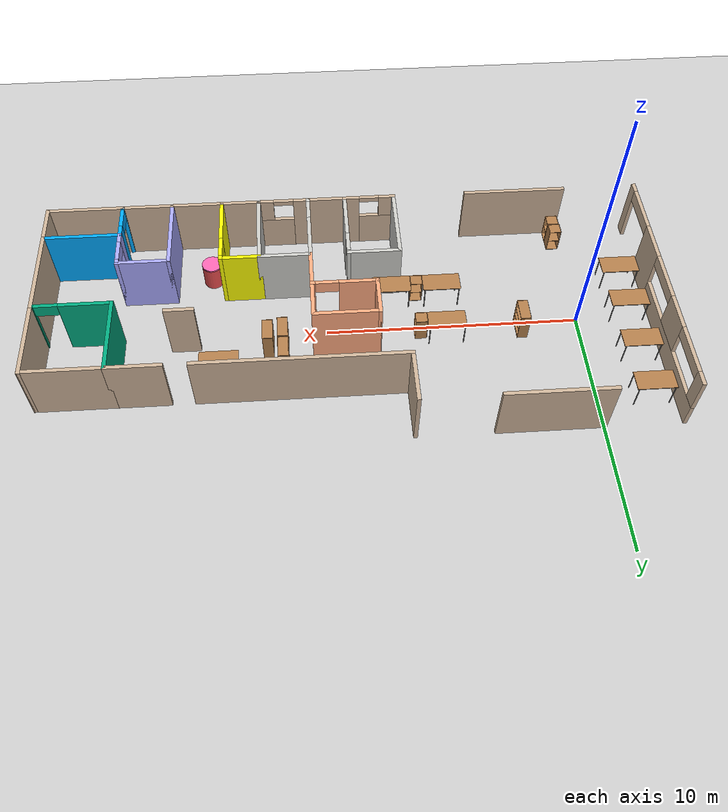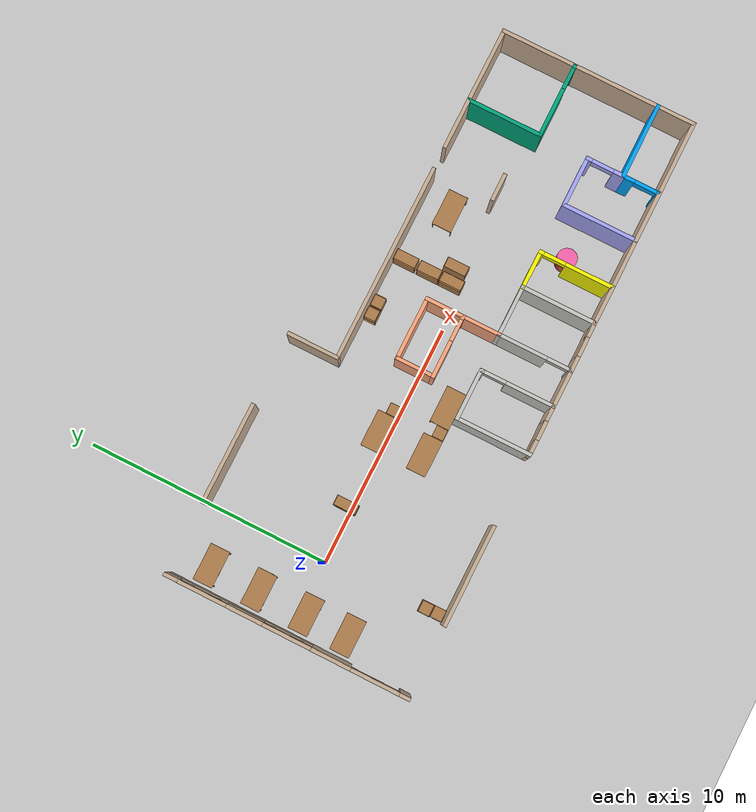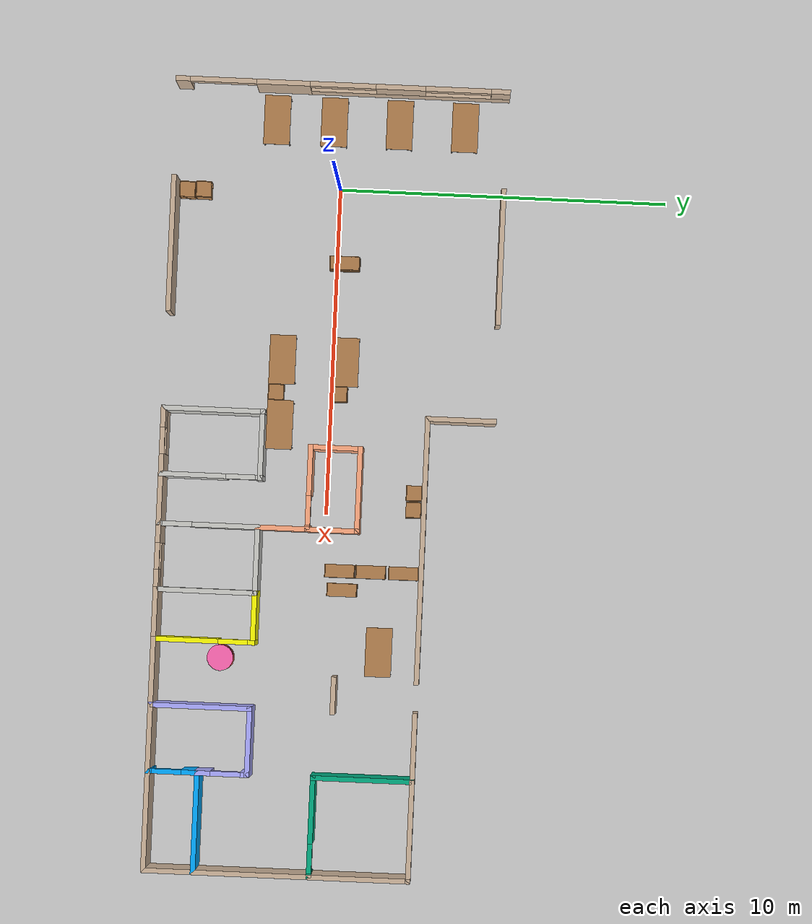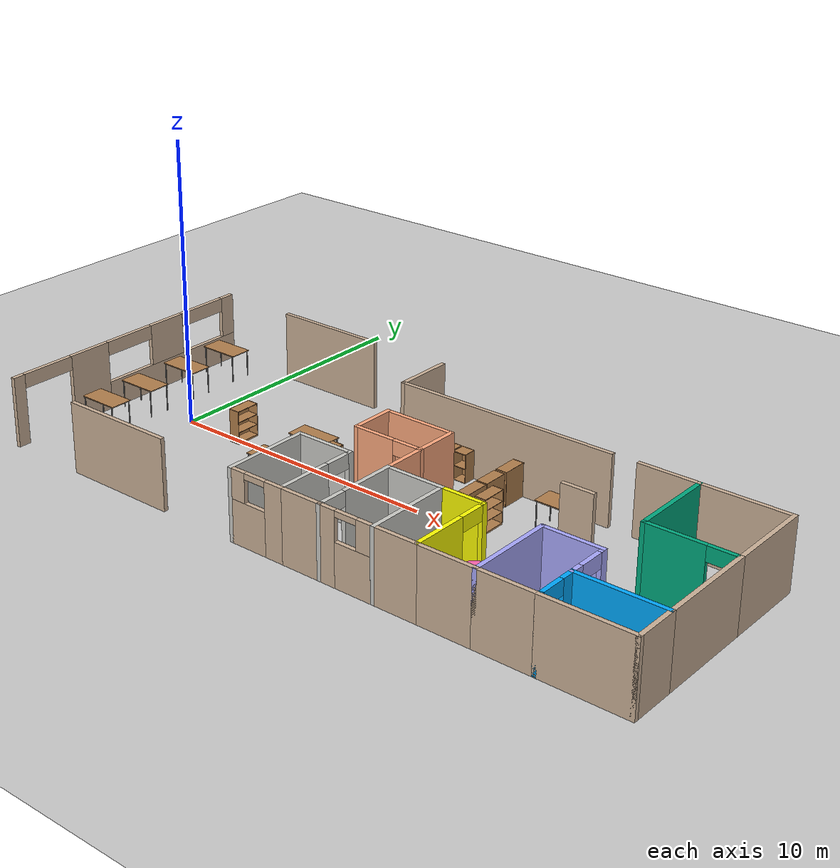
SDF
<sdf version="1.6">
 <world name="default">
  <light name="sun" type="directional">
   <pose>0 0 10 0 -0 0</pose>
   <diffuse>0.8 0.8 0.8 1</diffuse>
   <specular>0.2 0.2 0.2 1</specular>
   <attenuation>
    <range>1000</range>
    <constant>0.9</constant>
    <linear>0.01</linear>
    <quadratic>0.001</quadratic>
   </attenuation>
   <direction>-0.5 0.1 -0.9</direction>
  </light>
  <model name="ground_plane">
   <static>1</static>
   <link name="link">
    <collision name="collision">
     <geometry><plane><normal>0 0 1</normal><size>100 100</size></plane></geometry>
     <surface><friction><ode><mu>100</mu><mu2>50</mu2></ode></friction></surface>
    </collision>
    <visual name="visual">
     <cast_shadows>0</cast_shadows>
     <geometry><plane><normal>0 0 1</normal><size>100 100</size></plane></geometry>
     <material>
      <script><uri>file://media/materials/scripts/gazebo.material</uri><name>Gazebo/Grey</name></script>
     </material>
    </visual>
   </link>
  </model>
  <gravity>0 0 -9.8</gravity>
  <magnetic_field>6e-06 2.3e-05 -4.2e-05</magnetic_field>
  <atmosphere type="adiabatic"/>
  <physics name="default_physics" default="0" type="ode">
   <max_step_size>0.001</max_step_size>
   <real_time_factor>1</real_time_factor>
   <real_time_update_rate>1000</real_time_update_rate>
  </physics>
  <scene><ambient>0.4 0.4 0.4 1</ambient><background>0.7 0.7 0.7 1</background><shadows>1</shadows></scene>
  <spherical_coordinates>
   <surface_model>EARTH_WGS84</surface_model>
   <latitude_deg>0</latitude_deg>
   <longitude_deg>0</longitude_deg>
   <elevation>0</elevation>
   <heading_deg>0</heading_deg>
  </spherical_coordinates>
  <model name="restaurant_renato">
   <pose>9 0 0 0 -0 0</pose>
   <link name="Wall_1">
    <pose>-12 0 0 0 -0 1.5708</pose>
    <visual name="Wall_1_Visual_0">
     <pose>-4.85276 0 1.25 0 -0 0</pose>
     <geometry><box><size>0.444476 0.15 2.5</size></box></geometry>
     <material>
      <script><uri>file://media/materials/scripts/gazebo.material</uri><name>Gazebo/Grey</name></script>
      <ambient>0.8 0.7 0.6 1</ambient>
     </material>
     <meta><layer>0</layer></meta>
    </visual>
    <collision name="Wall_1_Collision_0">
     <geometry><box><size>0.444476 0.15 2.5</size></box></geometry>
     <pose>-4.85276 0 1.25 0 -0 0</pose>
    </collision>
    <visual name="Wall_1_Visual_1">
     <pose>-1.81526 0 1.25 0 -0 0</pose>
     <geometry><box><size>1.63052 0.15 2.5</size></box></geometry>
     <material>
      <script><uri>file://media/materials/scripts/gazebo.material</uri><name>Gazebo/Grey</name></script>
      <ambient>0.8 0.7 0.6 1</ambient>
     </material>
     <meta><layer>0</layer></meta>
    </visual>
    <collision name="Wall_1_Collision_1">
     <geometry><box><size>1.63052 0.15 2.5</size></box></geometry>
     <pose>-1.81526 0 1.25 0 -0 0</pose>
    </collision>
    <visual name="Wall_1_Visual_2">
     <pose>2.0375 0 0.5 0 -0 0</pose>
     <geometry><box><size>6.075 0.15 1</size></box></geometry>
     <material>
      <script><uri>file://media/materials/scripts/gazebo.material</uri><name>Gazebo/Grey</name></script>
      <ambient>0.8 0.7 0.6 1</ambient>
     </material>
     <meta><layer>0</layer></meta>
    </visual>
    <collision name="Wall_1_Collision_2">
     <geometry><box><size>6.075 0.15 1</size></box></geometry>
     <pose>2.0375 0 0.5 0 -0 0</pose>
    </collision>
    <visual name="Wall_1_Visual_3">
     <pose>1.75 0 1.75 0 -0 0</pose>
     <geometry><box><size>1.5 0.15 1.5</size></box></geometry>
     <material>
      <script><uri>file://media/materials/scripts/gazebo.material</uri><name>Gazebo/Grey</name></script>
      <ambient>0.8 0.7 0.6 1</ambient>
     </material>
     <meta><layer>0</layer></meta>
    </visual>
    <collision name="Wall_1_Collision_3">
     <geometry><box><size>1.5 0.15 1.5</size></box></geometry>
     <pose>1.75 0 1.75 0 -0 0</pose>
    </collision>
    <visual name="Wall_1_Visual_4">
     <pose>4.7875 0 1.75 0 -0 0</pose>
     <geometry><box><size>0.575 0.15 1.5</size></box></geometry>
     <material>
      <script><uri>file://media/materials/scripts/gazebo.material</uri><name>Gazebo/Grey</name></script>
      <ambient>0.8 0.7 0.6 1</ambient>
     </material>
     <meta><layer>0</layer></meta>
    </visual>
    <collision name="Wall_1_Collision_4">
     <geometry><box><size>0.575 0.15 1.5</size></box></geometry>
     <pose>4.7875 0 1.75 0 -0 0</pose>
    </collision>
    <visual name="Wall_1_Visual_5">
     <pose>-3.63052 0 2.25 0 -0 0</pose>
     <geometry><box><size>2 0.15 0.5</size></box></geometry>
     <material>
      <script><uri>file://media/materials/scripts/gazebo.material</uri><name>Gazebo/Grey</name></script>
      <ambient>0.8 0.7 0.6 1</ambient>
     </material>
     <meta><layer>0</layer></meta>
    </visual>
    <collision name="Wall_1_Collision_5">
     <geometry><box><size>2 0.15 0.5</size></box></geometry>
     <pose>-3.63052 0 2.25 0 -0 0</pose>
    </collision>
    <visual name="Wall_1_Visual_6">
     <pose>0 0 2.25 0 -0 0</pose>
     <geometry><box><size>2 0.15 0.5</size></box></geometry>
     <material>
      <script><uri>file://media/materials/scripts/gazebo.material</uri><name>Gazebo/Grey</name></script>
      <ambient>0.8 0.7 0.6 1</ambient>
     </material>
     <meta><layer>0</layer></meta>
    </visual>
    <collision name="Wall_1_Collision_6">
     <geometry><box><size>2 0.15 0.5</size></box></geometry>
     <pose>0 0 2.25 0 -0 0</pose>
    </collision>
    <visual name="Wall_1_Visual_7">
     <pose>3.5 0 2.25 0 -0 0</pose>
     <geometry><box><size>2 0.15 0.5</size></box></geometry>
     <material>
      <script><uri>file://media/materials/scripts/gazebo.material</uri><name>Gazebo/Grey</name></script>
      <ambient>0.8 0.7 0.6 1</ambient>
     </material>
     <meta><layer>0</layer></meta>
    </visual>
    <collision name="Wall_1_Collision_7">
     <geometry><box><size>2 0.15 0.5</size></box></geometry>
     <pose>3.5 0 2.25 0 -0 0</pose>
    </collision>
   </link>
   <link name="Wall_24">
    <collision name="Wall_24_Collision">
     <geometry><box><size>3.15 0.15 2.5</size></box></geometry>
     <pose>0 0 1.25 0 -0 0</pose>
    </collision>
    <visual name="Wall_24_Visual">
     <pose>0 0 1.25 0 -0 0</pose>
     <geometry><box><size>3.15 0.15 2.5</size></box></geometry>
     <material>
      <script><uri>file://media/materials/scripts/gazebo.material</uri><name>Gazebo/CeilingTiled</name></script>
      <ambient>1 0 0 1</ambient>
     </material>
     <meta><layer>0</layer></meta>
    </visual>
    <pose>-2 -3.5 0 0 -0 1.5708</pose>
   </link>
   <link name="Wall_25">
    <collision name="Wall_25_Collision">
     <geometry><box><size>2.15 0.15 2.5</size></box></geometry>
     <pose>0 0 1.25 0 -0 0</pose>
    </collision>
    <visual name="Wall_25_Visual">
     <pose>0 0 1.25 0 -0 0</pose>
     <geometry><box><size>2.15 0.15 2.5</size></box></geometry>
     <material>
      <script><uri>file://media/materials/scripts/gazebo.material</uri><name>Gazebo/CeilingTiled</name></script>
      <ambient>1 0 0 1</ambient>
     </material>
     <meta><layer>0</layer></meta>
    </visual>
    <pose>-1 -2 0 0 -0 0</pose>
   </link>
   <link name="Wall_26">
    <pose>0 -3.5 0 0 0 -1.5708</pose>
    <visual name="Wall_26_Visual_0">
     <pose>-1.47325 0 1.25 0 -0 0</pose>
     <geometry><box><size>0.203506 0.15 2.5</size></box></geometry>
     <material>
      <script><uri>file://media/materials/scripts/gazebo.material</uri><name>Gazebo/CeilingTiled</name></script>
      <ambient>1 0 0 1</ambient>
     </material>
     <meta><layer>0</layer></meta>
    </visual>
    <collision name="Wall_26_Collision_0">
     <geometry><box><size>0.203506 0.15 2.5</size></box></geometry>
     <pose>-1.47325 0 1.25 0 -0 0</pose>
    </collision>
    <visual name="Wall_26_Visual_1">
     <pose>0.551753 0 1.25 0 -0 0</pose>
     <geometry><box><size>2.04649 0.15 2.5</size></box></geometry>
     <material>
      <script><uri>file://media/materials/scripts/gazebo.material</uri><name>Gazebo/CeilingTiled</name></script>
      <ambient>1 0 0 1</ambient>
     </material>
     <meta><layer>0</layer></meta>
    </visual>
    <collision name="Wall_26_Collision_1">
     <geometry><box><size>2.04649 0.15 2.5</size></box></geometry>
     <pose>0.551753 0 1.25 0 -0 0</pose>
    </collision>
    <visual name="Wall_26_Visual_2">
     <pose>-0.921494 0 2.25 0 -0 0</pose>
     <geometry><box><size>0.9 0.15 0.5</size></box></geometry>
     <material>
      <script><uri>file://media/materials/scripts/gazebo.material</uri><name>Gazebo/CeilingTiled</name></script>
      <ambient>1 0 0 1</ambient>
     </material>
     <meta><layer>0</layer></meta>
    </visual>
    <collision name="Wall_26_Collision_2">
     <geometry><box><size>0.9 0.15 0.5</size></box></geometry>
     <pose>-0.921494 0 2.25 0 -0 0</pose>
    </collision>
   </link>
   <link name="Wall_27">
    <pose>-1 -5 0 0 -0 3.14159</pose>
    <visual name="Wall_27_Visual_0">
     <pose>-0.7375 0 1.25 0 -0 0</pose>
     <geometry><box><size>0.675 0.15 2.5</size></box></geometry>
     <material>
      <script><uri>file://media/materials/scripts/gazebo.material</uri><name>Gazebo/Grey</name></script>
      <ambient>0.8 0.7 0.6 1</ambient>
     </material>
     <meta><layer>0</layer></meta>
    </visual>
    <collision name="Wall_27_Collision_0">
     <geometry><box><size>0.675 0.15 2.5</size></box></geometry>
     <pose>-0.7375 0 1.25 0 -0 0</pose>
    </collision>
    <visual name="Wall_27_Visual_1">
     <pose>0.3375 0 0.75 0 -0 0</pose>
     <geometry><box><size>1.475 0.15 1.5</size></box></geometry>
     <material>
      <script><uri>file://media/materials/scripts/gazebo.material</uri><name>Gazebo/Grey</name></script>
      <ambient>0.8 0.7 0.6 1</ambient>
     </material>
     <meta><layer>0</layer></meta>
    </visual>
    <collision name="Wall_27_Collision_1">
     <geometry><box><size>1.475 0.15 1.5</size></box></geometry>
     <pose>0.3375 0 0.75 0 -0 0</pose>
    </collision>
    <visual name="Wall_27_Visual_2">
     <pose>0.7375 0 2 0 -0 0</pose>
     <geometry><box><size>0.675 0.15 1</size></box></geometry>
     <material>
      <script><uri>file://media/materials/scripts/gazebo.material</uri><name>Gazebo/Grey</name></script>
      <ambient>0.8 0.7 0.6 1</ambient>
     </material>
     <meta><layer>0</layer></meta>
    </visual>
    <collision name="Wall_27_Collision_2">
     <geometry><box><size>0.675 0.15 1</size></box></geometry>
     <pose>0.7375 0 2 0 -0 0</pose>
    </collision>
    <visual name="Wall_27_Visual_3">
     <pose>0 0 2.4 0 -0 0</pose>
     <geometry><box><size>0.8 0.15 0.2</size></box></geometry>
     <material>
      <script><uri>file://media/materials/scripts/gazebo.material</uri><name>Gazebo/Grey</name></script>
      <ambient>0.8 0.7 0.6 1</ambient>
     </material>
     <meta><layer>0</layer></meta>
    </visual>
    <collision name="Wall_27_Collision_3">
     <geometry><box><size>0.8 0.15 0.2</size></box></geometry>
     <pose>0 0 2.4 0 -0 0</pose>
    </collision>
   </link>
   <link name="Wall_29">
    <collision name="Wall_29_Collision">
     <geometry><box><size>1.65 0.15 2.5</size></box></geometry>
     <pose>0 0 1.25 0 -0 0</pose>
    </collision>
    <visual name="Wall_29_Visual">
     <pose>0 0 1.25 0 -0 0</pose>
     <geometry><box><size>1.65 0.15 2.5</size></box></geometry>
     <material>
      <script><uri>file://media/materials/scripts/gazebo.material</uri><name>Gazebo/Grey</name></script>
      <ambient>0.8 0.7 0.6 1</ambient>
     </material>
     <meta><layer>0</layer></meta>
    </visual>
    <pose>0.75 -5 0 0 -0 0</pose>
   </link>
   <link name="Wall_3">
    <collision name="Wall_3_Collision">
     <geometry><box><size>4.15 0.15 2.5</size></box></geometry>
     <pose>0 0 1.25 0 -0 0</pose>
    </collision>
    <visual name="Wall_3_Visual">
     <pose>0 0 1.25 0 -0 0</pose>
     <geometry><box><size>4.15 0.15 2.5</size></box></geometry>
     <material>
      <script><uri>file://media/materials/scripts/gazebo.material</uri><name>Gazebo/Grey</name></script>
      <ambient>0.8 0.7 0.6 1</ambient>
     </material>
     <meta><layer>0</layer></meta>
    </visual>
    <pose>-7 5 0 0 -0 0</pose>
   </link>
   <link name="Wall_30">
    <pose>1.5 -3.5 0 0 -0 1.5708</pose>
    <visual name="Wall_30_Visual_0">
     <pose>-1.48476 0 1.25 0 -0 0</pose>
     <geometry><box><size>0.18049 0.15 2.5</size></box></geometry>
     <material>
      <script><uri>file://media/materials/scripts/gazebo.material</uri><name>Gazebo/CeilingTiled</name></script>
      <ambient>1 0 0.498039 1</ambient>
     </material>
     <meta><layer>0</layer></meta>
    </visual>
    <collision name="Wall_30_Collision_0">
     <geometry><box><size>0.18049 0.15 2.5</size></box></geometry>
     <pose>-1.48476 0 1.25 0 -0 0</pose>
    </collision>
    <visual name="Wall_30_Visual_1">
     <pose>0.540245 0 1.25 0 -0 0</pose>
     <geometry><box><size>2.06951 0.15 2.5</size></box></geometry>
     <material>
      <script><uri>file://media/materials/scripts/gazebo.material</uri><name>Gazebo/CeilingTiled</name></script>
      <ambient>1 0 0.498039 1</ambient>
     </material>
     <meta><layer>0</layer></meta>
    </visual>
    <collision name="Wall_30_Collision_1">
     <geometry><box><size>2.06951 0.15 2.5</size></box></geometry>
     <pose>0.540245 0 1.25 0 -0 0</pose>
    </collision>
    <visual name="Wall_30_Visual_2">
     <pose>-0.94451 0 2.25 0 -0 0</pose>
     <geometry><box><size>0.9 0.15 0.5</size></box></geometry>
     <material>
      <script><uri>file://media/materials/scripts/gazebo.material</uri><name>Gazebo/CeilingTiled</name></script>
      <ambient>1 0 0.498039 1</ambient>
     </material>
     <meta><layer>0</layer></meta>
    </visual>
    <collision name="Wall_30_Collision_2">
     <geometry><box><size>0.9 0.15 0.5</size></box></geometry>
     <pose>-0.94451 0 2.25 0 -0 0</pose>
    </collision>
   </link>
   <link name="Wall_31">
    <collision name="Wall_31_Collision">
     <geometry><box><size>2.15048 0.15 2.5</size></box></geometry>
     <pose>0 0 1.25 0 -0 0</pose>
    </collision>
    <visual name="Wall_31_Visual">
     <pose>0 0 1.25 0 -0 0</pose>
     <geometry><box><size>2.15048 0.15 2.5</size></box></geometry>
     <material>
      <script><uri>file://media/materials/scripts/gazebo.material</uri><name>Gazebo/CeilingTiled</name></script>
      <ambient>1 0 0.498039 1</ambient>
     </material>
     <meta><layer>0</layer></meta>
    </visual>
    <pose>2.5 -2 0 0 -0 0</pose>
   </link>
   <link name="Wall_32">
    <collision name="Wall_32_Collision">
     <geometry><box><size>3.15 0.15 2.5</size></box></geometry>
     <pose>0 0 1.25 0 -0 0</pose>
    </collision>
    <visual name="Wall_32_Visual">
     <pose>0 0 1.25 0 -0 0</pose>
     <geometry><box><size>3.15 0.15 2.5</size></box></geometry>
     <material>
      <script><uri>file://media/materials/scripts/gazebo.material</uri><name>Gazebo/CeilingTiled</name></script>
      <ambient>1 0 0.498039 1</ambient>
     </material>
     <meta><layer>0</layer></meta>
    </visual>
    <pose>3.5 -3.5 0 0 0 -1.5708</pose>
   </link>
   <link name="Wall_36">
    <collision name="Wall_36_Collision">
     <geometry><box><size>1.65 0.15 2.5</size></box></geometry>
     <pose>0 0 1.25 0 -0 0</pose>
    </collision>
    <visual name="Wall_36_Visual">
     <pose>0 0 1.25 0 -0 0</pose>
     <geometry><box><size>1.65 0.15 2.5</size></box></geometry>
     <material>
      <script><uri>file://media/materials/scripts/gazebo.material</uri><name>Gazebo/Grey</name></script>
      <ambient>1 0.666667 0.498039 1</ambient>
     </material>
     <meta><layer>0</layer></meta>
    </visual>
    <pose>1.5 -1.25 0 0 -0 1.5708</pose>
   </link>
   <link name="Wall_37">
    <pose>0.25 -0.5 0 0 -0 3.14159</pose>
    <visual name="Wall_37_Visual_0">
     <pose>-1.22433 0 1.25 0 -0 0</pose>
     <geometry><box><size>0.201342 0.15 2.5</size></box></geometry>
     <material>
      <script><uri>file://media/materials/scripts/gazebo.material</uri><name>Gazebo/Grey</name></script>
      <ambient>1 0.666667 0.498039 1</ambient>
     </material>
     <meta><layer>0</layer></meta>
    </visual>
    <collision name="Wall_37_Collision_0">
     <geometry><box><size>0.201342 0.15 2.5</size></box></geometry>
     <pose>-1.22433 0 1.25 0 -0 0</pose>
    </collision>
    <visual name="Wall_37_Visual_1">
     <pose>0.550671 0 1.25 0 -0 0</pose>
     <geometry><box><size>1.54866 0.15 2.5</size></box></geometry>
     <material>
      <script><uri>file://media/materials/scripts/gazebo.material</uri><name>Gazebo/Grey</name></script>
      <ambient>1 0.666667 0.498039 1</ambient>
     </material>
     <meta><layer>0</layer></meta>
    </visual>
    <collision name="Wall_37_Collision_1">
     <geometry><box><size>1.54866 0.15 2.5</size></box></geometry>
     <pose>0.550671 0 1.25 0 -0 0</pose>
    </collision>
    <visual name="Wall_37_Visual_2">
     <pose>-0.673658 0 2.25 0 -0 0</pose>
     <geometry><box><size>0.9 0.15 0.5</size></box></geometry>
     <material>
      <script><uri>file://media/materials/scripts/gazebo.material</uri><name>Gazebo/Grey</name></script>
      <ambient>1 0.666667 0.498039 1</ambient>
     </material>
     <meta><layer>0</layer></meta>
    </visual>
    <collision name="Wall_37_Collision_2">
     <geometry><box><size>0.9 0.15 0.5</size></box></geometry>
     <pose>-0.673658 0 2.25 0 -0 0</pose>
    </collision>
   </link>
   <link name="Wall_38">
    <collision name="Wall_38_Collision">
     <geometry><box><size>1.65 0.15 2.5</size></box></geometry>
     <pose>0 0 1.25 0 -0 0</pose>
    </collision>
    <visual name="Wall_38_Visual">
     <pose>0 0 1.25 0 -0 0</pose>
     <geometry><box><size>1.65 0.15 2.5</size></box></geometry>
     <material>
      <script><uri>file://media/materials/scripts/gazebo.material</uri><name>Gazebo/Grey</name></script>
      <ambient>1 0.666667 0.498039 1</ambient>
     </material>
     <meta><layer>0</layer></meta>
    </visual>
    <pose>-1 0.25 0 0 -0 1.5708</pose>
   </link>
   <link name="Wall_39">
    <collision name="Wall_39_Collision">
     <geometry><box><size>2.65 0.15 2.5</size></box></geometry>
     <pose>0 0 1.25 0 -0 0</pose>
    </collision>
    <visual name="Wall_39_Visual">
     <pose>0 0 1.25 0 -0 0</pose>
     <geometry><box><size>2.65 0.15 2.5</size></box></geometry>
     <material>
      <script><uri>file://media/materials/scripts/gazebo.material</uri><name>Gazebo/Grey</name></script>
      <ambient>1 0.666667 0.498039 1</ambient>
     </material>
     <meta><layer>0</layer></meta>
    </visual>
    <pose>0.25 1 0 0 -0 0</pose>
   </link>
   <link name="Wall_40">
    <collision name="Wall_40_Collision">
     <geometry><box><size>1.65 0.15 2.5</size></box></geometry>
     <pose>0 0 1.25 0 -0 0</pose>
    </collision>
    <visual name="Wall_40_Visual">
     <pose>0 0 1.25 0 -0 0</pose>
     <geometry><box><size>1.65 0.15 2.5</size></box></geometry>
     <material>
      <script><uri>file://media/materials/scripts/gazebo.material</uri><name>Gazebo/Grey</name></script>
      <ambient>1 0.666667 0.498039 1</ambient>
     </material>
     <meta><layer>0</layer></meta>
    </visual>
    <pose>1.5 0.25 0 0 0 -1.5708</pose>
   </link>
   <link name="Wall_44">
    <collision name="Wall_44_Collision">
     <geometry><box><size>1.65 0.15 2.5</size></box></geometry>
     <pose>0 0 1.25 0 -0 0</pose>
    </collision>
    <visual name="Wall_44_Visual">
     <pose>0 0 1.25 0 -0 0</pose>
     <geometry><box><size>1.65 0.15 2.5</size></box></geometry>
     <material>
      <script><uri>file://media/materials/scripts/gazebo.material</uri><name>Gazebo/Grey</name></script>
      <ambient>1 1 0 1</ambient>
     </material>
     <meta><layer>0</layer></meta>
    </visual>
    <pose>4.25 -2 0 0 -0 0</pose>
   </link>
   <link name="Wall_45">
    <pose>5 -3.5 0 0 0 -1.5708</pose>
    <visual name="Wall_45_Visual_0">
     <pose>-1.46507 0 1.25 0 -0 0</pose>
     <geometry><box><size>0.219867 0.15 2.5</size></box></geometry>
     <material>
      <script><uri>file://media/materials/scripts/gazebo.material</uri><name>Gazebo/Grey</name></script>
      <ambient>1 1 0 1</ambient>
     </material>
     <meta><layer>0</layer></meta>
    </visual>
    <collision name="Wall_45_Collision_0">
     <geometry><box><size>0.219867 0.15 2.5</size></box></geometry>
     <pose>-1.46507 0 1.25 0 -0 0</pose>
    </collision>
    <visual name="Wall_45_Visual_1">
     <pose>0.559934 0 1.25 0 -0 0</pose>
     <geometry><box><size>2.03013 0.15 2.5</size></box></geometry>
     <material>
      <script><uri>file://media/materials/scripts/gazebo.material</uri><name>Gazebo/Grey</name></script>
      <ambient>1 1 0 1</ambient>
     </material>
     <meta><layer>0</layer></meta>
    </visual>
    <collision name="Wall_45_Collision_1">
     <geometry><box><size>2.03013 0.15 2.5</size></box></geometry>
     <pose>0.559934 0 1.25 0 -0 0</pose>
    </collision>
    <visual name="Wall_45_Visual_2">
     <pose>-0.905133 0 2.25 0 -0 0</pose>
     <geometry><box><size>0.9 0.15 0.5</size></box></geometry>
     <material>
      <script><uri>file://media/materials/scripts/gazebo.material</uri><name>Gazebo/Grey</name></script>
      <ambient>1 1 0 1</ambient>
     </material>
     <meta><layer>0</layer></meta>
    </visual>
    <collision name="Wall_45_Collision_2">
     <geometry><box><size>0.9 0.15 0.5</size></box></geometry>
     <pose>-0.905133 0 2.25 0 -0 0</pose>
    </collision>
   </link>
   <link name="Wall_46">
    <collision name="Wall_46_Collision">
     <geometry><box><size>1.65 0.15 2.5</size></box></geometry>
     <pose>0 0 1.25 0 -0 0</pose>
    </collision>
    <visual name="Wall_46_Visual">
     <pose>0 0 1.25 0 -0 0</pose>
     <geometry><box><size>1.65 0.15 2.5</size></box></geometry>
     <material>
      <script><uri>file://media/materials/scripts/gazebo.material</uri><name>Gazebo/Grey</name></script>
      <ambient>0.8 0.7 0.6 1</ambient>
     </material>
     <meta><layer>0</layer></meta>
    </visual>
    <pose>4.25 -5 0 0 -0 3.14159</pose>
   </link>
   <link name="Wall_48">
    <collision name="Wall_48_Collision">
     <geometry><box><size>2.15 0.15 2.5</size></box></geometry>
     <pose>0 0 1.25 0 -0 0</pose>
    </collision>
    <visual name="Wall_48_Visual">
     <pose>0 0 1.25 0 -0 0</pose>
     <geometry><box><size>2.15 0.15 2.5</size></box></geometry>
     <material>
      <script><uri>file://media/materials/scripts/gazebo.material</uri><name>Gazebo/Grey</name></script>
      <ambient>0.8 0.7 0.6 1</ambient>
     </material>
     <meta><layer>0</layer></meta>
    </visual>
    <pose>6 -5 0 0 -0 0</pose>
   </link>
   <link name="Wall_55">
    <collision name="Wall_55_Collision">
     <geometry><box><size>1.15 0.15 2.5</size></box></geometry>
     <pose>0 0 1.25 0 -0 0</pose>
    </collision>
    <visual name="Wall_55_Visual">
     <pose>0 0 1.25 0 -0 0</pose>
     <geometry><box><size>1.15 0.15 2.5</size></box></geometry>
     <material>
      <script><uri>file://media/materials/scripts/gazebo.material</uri><name>Gazebo/Grey</name></script>
      <ambient>0.8 0.7 0.6 1</ambient>
     </material>
     <meta><layer>0</layer></meta>
    </visual>
    <pose>6.5 0.5 0 0 -0 0</pose>
   </link>
   <link name="Wall_57">
    <collision name="Wall_57_Collision">
     <geometry><box><size>2.15 0.15 2.5</size></box></geometry>
     <pose>0 0 1.25 0 -0 0</pose>
    </collision>
    <visual name="Wall_57_Visual">
     <pose>0 0 1.25 0 -0 0</pose>
     <geometry><box><size>2.15 0.15 2.5</size></box></geometry>
     <material>
      <script><uri>file://media/materials/scripts/gazebo.material</uri><name>Gazebo/Grey</name></script>
      <ambient>0.8 0.7 0.6 1</ambient>
     </material>
     <meta><layer>0</layer></meta>
    </visual>
    <pose>8 3 0 0 -0 0</pose>
   </link>
   <link name="Wall_6">
    <collision name="Wall_6_Collision">
     <geometry><box><size>4.15 0.15 2.5</size></box></geometry>
     <pose>0 0 1.25 0 -0 0</pose>
    </collision>
    <visual name="Wall_6_Visual">
     <pose>0 0 1.25 0 -0 0</pose>
     <geometry><box><size>4.15 0.15 2.5</size></box></geometry>
     <material>
      <script><uri>file://media/materials/scripts/gazebo.material</uri><name>Gazebo/Grey</name></script>
      <ambient>0.8 0.7 0.6 1</ambient>
     </material>
     <meta><layer>0</layer></meta>
    </visual>
    <pose>-7 -5 0 0 -0 0</pose>
   </link>
   <link name="Wall_60">
    <collision name="Wall_60_Collision">
     <geometry><box><size>3.15 0.15 2.5</size></box></geometry>
     <pose>0 0 1.25 0 -0 0</pose>
    </collision>
    <visual name="Wall_60_Visual">
     <pose>0 0 1.25 0 -0 0</pose>
     <geometry><box><size>3.15 0.15 2.5</size></box></geometry>
     <material>
      <script><uri>file://media/materials/scripts/gazebo.material</uri><name>Gazebo/Grey</name></script>
      <ambient>0.666667 0.666667 1 1</ambient>
     </material>
     <meta><layer>0</layer></meta>
    </visual>
    <pose>7 -3.5 0 0 -0 1.5708</pose>
   </link>
   <link name="Wall_64">
    <pose>10.5 0 0 0 -0 3.14159</pose>
    <visual name="Wall_64_Visual_0">
     <pose>-1.48453 0 1.25 0 -0 0</pose>
     <geometry><box><size>0.180937 0.15 2.5</size></box></geometry>
     <material>
      <script><uri>file://media/materials/scripts/gazebo.material</uri><name>Gazebo/Grey</name></script>
      <ambient>0 0.666667 0.498039 1</ambient>
     </material>
     <meta><layer>0</layer></meta>
    </visual>
    <collision name="Wall_64_Collision_0">
     <geometry><box><size>0.180937 0.15 2.5</size></box></geometry>
     <pose>-1.48453 0 1.25 0 -0 0</pose>
    </collision>
    <visual name="Wall_64_Visual_1">
     <pose>0.540468 0 1.25 0 -0 0</pose>
     <geometry><box><size>2.06906 0.15 2.5</size></box></geometry>
     <material>
      <script><uri>file://media/materials/scripts/gazebo.material</uri><name>Gazebo/Grey</name></script>
      <ambient>0 0.666667 0.498039 1</ambient>
     </material>
     <meta><layer>0</layer></meta>
    </visual>
    <collision name="Wall_64_Collision_1">
     <geometry><box><size>2.06906 0.15 2.5</size></box></geometry>
     <pose>0.540468 0 1.25 0 -0 0</pose>
    </collision>
    <visual name="Wall_64_Visual_2">
     <pose>-0.944063 0 2.25 0 -0 0</pose>
     <geometry><box><size>0.9 0.15 0.5</size></box></geometry>
     <material>
      <script><uri>file://media/materials/scripts/gazebo.material</uri><name>Gazebo/Grey</name></script>
      <ambient>0 0.666667 0.498039 1</ambient>
     </material>
     <meta><layer>0</layer></meta>
    </visual>
    <collision name="Wall_64_Collision_2">
     <geometry><box><size>0.9 0.15 0.5</size></box></geometry>
     <pose>-0.944063 0 2.25 0 -0 0</pose>
    </collision>
   </link>
   <link name="Wall_66">
    <collision name="Wall_66_Collision">
     <geometry><box><size>3.15 0.15 2.5</size></box></geometry>
     <pose>0 0 1.25 0 -0 0</pose>
    </collision>
    <visual name="Wall_66_Visual">
     <pose>0 0 1.25 0 -0 0</pose>
     <geometry><box><size>3.15 0.15 2.5</size></box></geometry>
     <material>
      <script><uri>file://media/materials/scripts/gazebo.material</uri><name>Gazebo/Grey</name></script>
      <ambient>0 0.666667 0.498039 1</ambient>
     </material>
     <meta><layer>0</layer></meta>
    </visual>
    <pose>9 1.5 0 0 0 -1.5708</pose>
   </link>
   <link name="Wall_68">
    <collision name="Wall_68_Collision">
     <geometry><box><size>2.15 0.15 2.5</size></box></geometry>
     <pose>0 0 1.25 0 -0 0</pose>
    </collision>
    <visual name="Wall_68_Visual">
     <pose>0 0 1.25 0 -0 0</pose>
     <geometry><box><size>2.15 0.15 2.5</size></box></geometry>
     <material>
      <script><uri>file://media/materials/scripts/gazebo.material</uri><name>Gazebo/Grey</name></script>
      <ambient>0.666667 0.666667 1 1</ambient>
     </material>
     <meta><layer>0</layer></meta>
    </visual>
    <pose>8 -2 0 0 -0 0</pose>
   </link>
   <link name="Wall_71">
    <collision name="Wall_71_Collision">
     <geometry><box><size>2.15 0.15 2.5</size></box></geometry>
     <pose>0 0 1.25 0 -0 0</pose>
    </collision>
    <visual name="Wall_71_Visual">
     <pose>0 0 1.25 0 -0 0</pose>
     <geometry><box><size>2.15 0.15 2.5</size></box></geometry>
     <material>
      <script><uri>file://media/materials/scripts/gazebo.material</uri><name>Gazebo/Grey</name></script>
      <ambient>0.8 0.7 0.6 1</ambient>
     </material>
     <meta><layer>0</layer></meta>
    </visual>
    <pose>8 -5 0 0 -0 0</pose>
   </link>
   <link name="Wall_72">
    <collision name="Wall_72_Collision">
     <geometry><box><size>0.15 0.15 2.5</size></box></geometry>
     <pose>0 0 1.25 0 -0 0</pose>
    </collision>
    <visual name="Wall_72_Visual">
     <pose>0 0 1.25 0 -0 0</pose>
     <geometry><box><size>0.15 0.15 2.5</size></box></geometry>
     <material>
      <script><uri>file://media/materials/scripts/gazebo.material</uri><name>Gazebo/Grey</name></script>
      <ambient>1 1 1 1</ambient>
     </material>
     <meta><layer>0</layer></meta>
    </visual>
    <pose>9 -5 0 0 -0 0</pose>
   </link>
   <link name="Wall_73">
    <collision name="Wall_73_Collision">
     <geometry><box><size>3.15 0.15 2.5</size></box></geometry>
     <pose>0 0 1.25 0 -0 0</pose>
    </collision>
    <visual name="Wall_73_Visual">
     <pose>0 0 1.25 0 -0 0</pose>
     <geometry><box><size>3.15 0.15 2.5</size></box></geometry>
     <material>
      <script><uri>file://media/materials/scripts/gazebo.material</uri><name>Gazebo/Grey</name></script>
      <ambient>0.8 0.7 0.6 1</ambient>
     </material>
     <meta><layer>0</layer></meta>
    </visual>
    <pose>10.5 -5 0 0 -0 0</pose>
   </link>
   <link name="Wall_75">
    <pose>9 -2.75 0 0 0 -1.5708</pose>
    <visual name="Wall_75_Visual_0">
     <pose>-0.6875 0 1.25 0 -0 0</pose>
     <geometry><box><size>0.275 0.15 2.5</size></box></geometry>
     <material>
      <script><uri>file://media/materials/scripts/gazebo.material</uri><name>Gazebo/Grey</name></script>
      <ambient>0.666667 0.666667 1 1</ambient>
     </material>
     <meta><layer>0</layer></meta>
    </visual>
    <collision name="Wall_75_Collision_0">
     <geometry><box><size>0.275 0.15 2.5</size></box></geometry>
     <pose>-0.6875 0 1.25 0 -0 0</pose>
    </collision>
    <visual name="Wall_75_Visual_1">
     <pose>0.5875 0 1.25 0 -0 0</pose>
     <geometry><box><size>0.475 0.15 2.5</size></box></geometry>
     <material>
      <script><uri>file://media/materials/scripts/gazebo.material</uri><name>Gazebo/Grey</name></script>
      <ambient>0.666667 0.666667 1 1</ambient>
     </material>
     <meta><layer>0</layer></meta>
    </visual>
    <collision name="Wall_75_Collision_1">
     <geometry><box><size>0.475 0.15 2.5</size></box></geometry>
     <pose>0.5875 0 1.25 0 -0 0</pose>
    </collision>
    <visual name="Wall_75_Visual_2">
     <pose>-0.1 0 2.25 0 -0 0</pose>
     <geometry><box><size>0.9 0.15 0.5</size></box></geometry>
     <material>
      <script><uri>file://media/materials/scripts/gazebo.material</uri><name>Gazebo/Grey</name></script>
      <ambient>0.666667 0.666667 1 1</ambient>
     </material>
     <meta><layer>0</layer></meta>
    </visual>
    <collision name="Wall_75_Collision_2">
     <geometry><box><size>0.9 0.15 0.5</size></box></geometry>
     <pose>-0.1 0 2.25 0 -0 0</pose>
    </collision>
   </link>
   <link name="Wall_76">
    <pose>9 -4.25 0 0 0 -1.5708</pose>
    <visual name="Wall_76_Visual_0">
     <pose>-0.54736 0 1.25 0 -0 0</pose>
     <geometry><box><size>0.555281 0.15 2.5</size></box></geometry>
     <material>
      <script><uri>file://media/materials/scripts/gazebo.material</uri><name>Gazebo/Grey</name></script>
      <ambient>0 0.666667 1 1</ambient>
     </material>
     <meta><layer>0</layer></meta>
    </visual>
    <collision name="Wall_76_Collision_0">
     <geometry><box><size>0.555281 0.15 2.5</size></box></geometry>
     <pose>-0.54736 0 1.25 0 -0 0</pose>
    </collision>
    <visual name="Wall_76_Visual_1">
     <pose>0.72764 0 1.25 0 -0 0</pose>
     <geometry><box><size>0.194719 0.15 2.5</size></box></geometry>
     <material>
      <script><uri>file://media/materials/scripts/gazebo.material</uri><name>Gazebo/Grey</name></script>
      <ambient>0 0.666667 1 1</ambient>
     </material>
     <meta><layer>0</layer></meta>
    </visual>
    <collision name="Wall_76_Collision_1">
     <geometry><box><size>0.194719 0.15 2.5</size></box></geometry>
     <pose>0.72764 0 1.25 0 -0 0</pose>
    </collision>
    <visual name="Wall_76_Visual_2">
     <pose>0.180281 0 2.25 0 -0 0</pose>
     <geometry><box><size>0.9 0.15 0.5</size></box></geometry>
     <material>
      <script><uri>file://media/materials/scripts/gazebo.material</uri><name>Gazebo/Grey</name></script>
      <ambient>0 0.666667 1 1</ambient>
     </material>
     <meta><layer>0</layer></meta>
    </visual>
    <collision name="Wall_76_Collision_2">
     <geometry><box><size>0.9 0.15 0.5</size></box></geometry>
     <pose>0.180281 0 2.25 0 -0 0</pose>
    </collision>
   </link>
   <link name="Wall_78">
    <collision name="Wall_78_Collision">
     <geometry><box><size>3.15 0.15 2.5</size></box></geometry>
     <pose>0 0 1.25 0 -0 0</pose>
    </collision>
    <visual name="Wall_78_Visual">
     <pose>0 0 1.25 0 -0 0</pose>
     <geometry><box><size>3.15 0.15 2.5</size></box></geometry>
     <material>
      <script><uri>file://media/materials/scripts/gazebo.material</uri><name>Gazebo/Grey</name></script>
      <ambient>0 0.666667 1 1</ambient>
     </material>
     <meta><layer>0</layer></meta>
    </visual>
    <pose>10.5 -3.5 0 0 -0 0</pose>
   </link>
   <link name="Wall_80">
    <collision name="Wall_80_Collision">
     <geometry><box><size>1.65 0.15 2.5</size></box></geometry>
     <pose>0 0 1.25 0 -0 0</pose>
    </collision>
    <visual name="Wall_80_Visual">
     <pose>0 0 1.25 0 -0 0</pose>
     <geometry><box><size>1.65 0.15 2.5</size></box></geometry>
     <material>
      <script><uri>file://media/materials/scripts/gazebo.material</uri><name>Gazebo/Grey</name></script>
      <ambient>0.8 0.7 0.6 1</ambient>
     </material>
     <meta><layer>0</layer></meta>
    </visual>
    <pose>12 -4.25 0 0 0 -1.5708</pose>
   </link>
   <link name="Wall_82">
    <collision name="Wall_82_Collision">
     <geometry><box><size>3.65 0.15 2.5</size></box></geometry>
     <pose>0 0 1.25 0 -0 0</pose>
    </collision>
    <visual name="Wall_82_Visual">
     <pose>0 0 1.25 0 -0 0</pose>
     <geometry><box><size>3.65 0.15 2.5</size></box></geometry>
     <material>
      <script><uri>file://media/materials/scripts/gazebo.material</uri><name>Gazebo/Grey</name></script>
      <ambient>0.8 0.7 0.6 1</ambient>
     </material>
     <meta><layer>0</layer></meta>
    </visual>
    <pose>12 -1.75 0 0 0 -1.5708</pose>
   </link>
   <link name="Wall_86">
    <pose>2.5 -5 0 0 -0 0</pose>
    <visual name="Wall_86_Visual_0">
     <pose>-0.7375 0 1.25 0 -0 0</pose>
     <geometry><box><size>0.675 0.15 2.5</size></box></geometry>
     <material>
      <script><uri>file://media/materials/scripts/gazebo.material</uri><name>Gazebo/Grey</name></script>
      <ambient>0.8 0.7 0.6 1</ambient>
     </material>
     <meta><layer>0</layer></meta>
    </visual>
    <collision name="Wall_86_Collision_0">
     <geometry><box><size>0.675 0.15 2.5</size></box></geometry>
     <pose>-0.7375 0 1.25 0 -0 0</pose>
    </collision>
    <visual name="Wall_86_Visual_1">
     <pose>0.3375 0 0.75 0 -0 0</pose>
     <geometry><box><size>1.475 0.15 1.5</size></box></geometry>
     <material>
      <script><uri>file://media/materials/scripts/gazebo.material</uri><name>Gazebo/Grey</name></script>
      <ambient>0.8 0.7 0.6 1</ambient>
     </material>
     <meta><layer>0</layer></meta>
    </visual>
    <collision name="Wall_86_Collision_1">
     <geometry><box><size>1.475 0.15 1.5</size></box></geometry>
     <pose>0.3375 0 0.75 0 -0 0</pose>
    </collision>
    <visual name="Wall_86_Visual_2">
     <pose>0.7375 0 2 0 -0 0</pose>
     <geometry><box><size>0.675 0.15 1</size></box></geometry>
     <material>
      <script><uri>file://media/materials/scripts/gazebo.material</uri><name>Gazebo/Grey</name></script>
      <ambient>0.8 0.7 0.6 1</ambient>
     </material>
     <meta><layer>0</layer></meta>
    </visual>
    <collision name="Wall_86_Collision_2">
     <geometry><box><size>0.675 0.15 1</size></box></geometry>
     <pose>0.7375 0 2 0 -0 0</pose>
    </collision>
    <visual name="Wall_86_Visual_3">
     <pose>0 0 2.4 0 -0 0</pose>
     <geometry><box><size>0.8 0.15 0.2</size></box></geometry>
     <material>
      <script><uri>file://media/materials/scripts/gazebo.material</uri><name>Gazebo/Grey</name></script>
      <ambient>0.8 0.7 0.6 1</ambient>
     </material>
     <meta><layer>0</layer></meta>
    </visual>
    <collision name="Wall_86_Collision_3">
     <geometry><box><size>0.8 0.15 0.2</size></box></geometry>
     <pose>0 0 2.4 0 -0 0</pose>
    </collision>
   </link>
   <link name="Wall_88">
    <collision name="Wall_88_Collision">
     <geometry><box><size>2.15 0.15 2.5</size></box></geometry>
     <pose>0 0 1.25 0 -0 0</pose>
    </collision>
    <visual name="Wall_88_Visual">
     <pose>0 0 1.25 0 -0 0</pose>
     <geometry><box><size>2.15 0.15 2.5</size></box></geometry>
     <material>
      <script><uri>file://media/materials/scripts/gazebo.material</uri><name>Gazebo/Grey</name></script>
      <ambient>0.8 0.7 0.6 1</ambient>
     </material>
     <meta><layer>0</layer></meta>
    </visual>
    <pose>-2 4 0 0 0 -1.5708</pose>
   </link>
   <link name="Wall_89">
    <collision name="Wall_89_Collision">
     <geometry><box><size>8.15 0.15 2.5</size></box></geometry>
     <pose>0 0 1.25 0 -0 0</pose>
    </collision>
    <visual name="Wall_89_Visual">
     <pose>0 0 1.25 0 -0 0</pose>
     <geometry><box><size>8.15 0.15 2.5</size></box></geometry>
     <material>
      <script><uri>file://media/materials/scripts/gazebo.material</uri><name>Gazebo/Grey</name></script>
      <ambient>0.8 0.7 0.6 1</ambient>
     </material>
     <meta><layer>0</layer></meta>
    </visual>
    <pose>2 3 0 0 -0 0</pose>
   </link>
   <link name="Wall_91">
    <collision name="Wall_91_Collision">
     <geometry><box><size>3.15 0.15 2.5</size></box></geometry>
     <pose>0 0 1.25 0 -0 0</pose>
    </collision>
    <visual name="Wall_91_Visual">
     <pose>0 0 1.25 0 -0 0</pose>
     <geometry><box><size>3.15 0.15 2.5</size></box></geometry>
     <material>
      <script><uri>file://media/materials/scripts/gazebo.material</uri><name>Gazebo/Grey</name></script>
      <ambient>0.8 0.7 0.6 1</ambient>
     </material>
     <meta><layer>0</layer></meta>
    </visual>
    <pose>10.5 3 0 0 -0 0</pose>
   </link>
   <link name="Wall_92">
    <collision name="Wall_92_Collision">
     <geometry><box><size>3.15 0.15 2.5</size></box></geometry>
     <pose>0 0 1.25 0 -0 0</pose>
    </collision>
    <visual name="Wall_92_Visual">
     <pose>0 0 1.25 0 -0 0</pose>
     <geometry><box><size>3.15 0.15 2.5</size></box></geometry>
     <material>
      <script><uri>file://media/materials/scripts/gazebo.material</uri><name>Gazebo/Grey</name></script>
      <ambient>0.8 0.7 0.6 1</ambient>
     </material>
     <meta><layer>0</layer></meta>
    </visual>
    <pose>12 1.5 0 0 0 -1.5708</pose>
   </link>
   <static>1</static>
  </model>
  <model name="table_clone">
   <static>1</static>
   <link name="link">
    <collision name="surface">
     <pose>0 0 1 0 -0 0</pose>
     <geometry><box><size>1.5 0.8 0.03</size></box></geometry>
     <surface><friction><ode><mu>0.6</mu><mu2>0.6</mu2></ode></friction></surface>
    </collision>
    <visual name="visual1">
     <pose>0 0 1 0 -0 0</pose>
     <geometry><box><size>1.5 0.8 0.03</size></box></geometry>
     <material>
      <script><uri>file://media/materials/scripts/gazebo.material</uri><name>Gazebo/Wood</name></script>
     </material>
    </visual>
    <collision name="front_left_leg">
     <pose>0.68 0.38 0.5 0 -0 0</pose>
     <geometry><cylinder><radius>0.02</radius><length>1</length></cylinder></geometry>
    </collision>
    <visual name="front_left_leg">
     <pose>0.68 0.38 0.5 0 -0 0</pose>
     <geometry><cylinder><radius>0.02</radius><length>1</length></cylinder></geometry>
     <material>
      <script><uri>file://media/materials/scripts/gazebo.material</uri><name>Gazebo/Grey</name></script>
     </material>
    </visual>
    <collision name="front_right_leg">
     <pose>0.68 -0.38 0.5 0 -0 0</pose>
     <geometry><cylinder><radius>0.02</radius><length>1</length></cylinder></geometry>
    </collision>
    <visual name="front_right_leg">
     <pose>0.68 -0.38 0.5 0 -0 0</pose>
     <geometry><cylinder><radius>0.02</radius><length>1</length></cylinder></geometry>
     <material>
      <script><uri>file://media/materials/scripts/gazebo.material</uri><name>Gazebo/Grey</name></script>
     </material>
    </visual>
    <collision name="back_right_leg">
     <pose>-0.68 -0.38 0.5 0 -0 0</pose>
     <geometry><cylinder><radius>0.02</radius><length>1</length></cylinder></geometry>
    </collision>
    <visual name="back_right_leg">
     <pose>-0.68 -0.38 0.5 0 -0 0</pose>
     <geometry><cylinder><radius>0.02</radius><length>1</length></cylinder></geometry>
     <material>
      <script><uri>file://media/materials/scripts/gazebo.material</uri><name>Gazebo/Grey</name></script>
     </material>
    </visual>
    <collision name="back_left_leg">
     <pose>-0.68 0.38 0.5 0 -0 0</pose>
     <geometry><cylinder><radius>0.02</radius><length>1</length></cylinder></geometry>
    </collision>
    <visual name="back_left_leg">
     <pose>-0.68 0.38 0.5 0 -0 0</pose>
     <geometry><cylinder><radius>0.02</radius><length>1</length></cylinder></geometry>
     <material>
      <script><uri>file://media/materials/scripts/gazebo.material</uri><name>Gazebo/Grey</name></script>
     </material>
    </visual>
   </link>
   <pose>-2 1.75 0 0 -0 0</pose>
  </model>
  <model name="table_clone_0">
   <static>1</static>
   <link name="link">
    <collision name="surface">
     <pose>0 0 1 0 -0 0</pose>
     <geometry><box><size>1.5 0.8 0.03</size></box></geometry>
     <surface><friction><ode><mu>0.6</mu><mu2>0.6</mu2></ode></friction></surface>
    </collision>
    <visual name="visual1">
     <pose>0 0 1 0 -0 0</pose>
     <geometry><box><size>1.5 0.8 0.03</size></box></geometry>
     <material>
      <script><uri>file://media/materials/scripts/gazebo.material</uri><name>Gazebo/Wood</name></script>
     </material>
    </visual>
    <collision name="front_left_leg">
     <pose>0.68 0.38 0.5 0 -0 0</pose>
     <geometry><cylinder><radius>0.02</radius><length>1</length></cylinder></geometry>
    </collision>
    <visual name="front_left_leg">
     <pose>0.68 0.38 0.5 0 -0 0</pose>
     <geometry><cylinder><radius>0.02</radius><length>1</length></cylinder></geometry>
     <material>
      <script><uri>file://media/materials/scripts/gazebo.material</uri><name>Gazebo/Grey</name></script>
     </material>
    </visual>
    <collision name="front_right_leg">
     <pose>0.68 -0.38 0.5 0 -0 0</pose>
     <geometry><cylinder><radius>0.02</radius><length>1</length></cylinder></geometry>
    </collision>
    <visual name="front_right_leg">
     <pose>0.68 -0.38 0.5 0 -0 0</pose>
     <geometry><cylinder><radius>0.02</radius><length>1</length></cylinder></geometry>
     <material>
      <script><uri>file://media/materials/scripts/gazebo.material</uri><name>Gazebo/Grey</name></script>
     </material>
    </visual>
    <collision name="back_right_leg">
     <pose>-0.68 -0.38 0.5 0 -0 0</pose>
     <geometry><cylinder><radius>0.02</radius><length>1</length></cylinder></geometry>
    </collision>
    <visual name="back_right_leg">
     <pose>-0.68 -0.38 0.5 0 -0 0</pose>
     <geometry><cylinder><radius>0.02</radius><length>1</length></cylinder></geometry>
     <material>
      <script><uri>file://media/materials/scripts/gazebo.material</uri><name>Gazebo/Grey</name></script>
     </material>
    </visual>
    <collision name="back_left_leg">
     <pose>-0.68 0.38 0.5 0 -0 0</pose>
     <geometry><cylinder><radius>0.02</radius><length>1</length></cylinder></geometry>
    </collision>
    <visual name="back_left_leg">
     <pose>-0.68 0.38 0.5 0 -0 0</pose>
     <geometry><cylinder><radius>0.02</radius><length>1</length></cylinder></geometry>
     <material>
      <script><uri>file://media/materials/scripts/gazebo.material</uri><name>Gazebo/Grey</name></script>
     </material>
    </visual>
   </link>
   <pose>-2 3.75 0 0 -0 0</pose>
  </model>
  <model name="table_clone_1">
   <static>1</static>
   <link name="link">
    <collision name="surface">
     <pose>0 0 1 0 -0 0</pose>
     <geometry><box><size>1.5 0.8 0.03</size></box></geometry>
     <surface><friction><ode><mu>0.6</mu><mu2>0.6</mu2></ode></friction></surface>
    </collision>
    <visual name="visual1">
     <pose>0 0 1 0 -0 0</pose>
     <geometry><box><size>1.5 0.8 0.03</size></box></geometry>
     <material>
      <script><uri>file://media/materials/scripts/gazebo.material</uri><name>Gazebo/Wood</name></script>
     </material>
    </visual>
    <collision name="front_left_leg">
     <pose>0.68 0.38 0.5 0 -0 0</pose>
     <geometry><cylinder><radius>0.02</radius><length>1</length></cylinder></geometry>
    </collision>
    <visual name="front_left_leg">
     <pose>0.68 0.38 0.5 0 -0 0</pose>
     <geometry><cylinder><radius>0.02</radius><length>1</length></cylinder></geometry>
     <material>
      <script><uri>file://media/materials/scripts/gazebo.material</uri><name>Gazebo/Grey</name></script>
     </material>
    </visual>
    <collision name="front_right_leg">
     <pose>0.68 -0.38 0.5 0 -0 0</pose>
     <geometry><cylinder><radius>0.02</radius><length>1</length></cylinder></geometry>
    </collision>
    <visual name="front_right_leg">
     <pose>0.68 -0.38 0.5 0 -0 0</pose>
     <geometry><cylinder><radius>0.02</radius><length>1</length></cylinder></geometry>
     <material>
      <script><uri>file://media/materials/scripts/gazebo.material</uri><name>Gazebo/Grey</name></script>
     </material>
    </visual>
    <collision name="back_right_leg">
     <pose>-0.68 -0.38 0.5 0 -0 0</pose>
     <geometry><cylinder><radius>0.02</radius><length>1</length></cylinder></geometry>
    </collision>
    <visual name="back_right_leg">
     <pose>-0.68 -0.38 0.5 0 -0 0</pose>
     <geometry><cylinder><radius>0.02</radius><length>1</length></cylinder></geometry>
     <material>
      <script><uri>file://media/materials/scripts/gazebo.material</uri><name>Gazebo/Grey</name></script>
     </material>
    </visual>
    <collision name="back_left_leg">
     <pose>-0.68 0.38 0.5 0 -0 0</pose>
     <geometry><cylinder><radius>0.02</radius><length>1</length></cylinder></geometry>
    </collision>
    <visual name="back_left_leg">
     <pose>-0.68 0.38 0.5 0 -0 0</pose>
     <geometry><cylinder><radius>0.02</radius><length>1</length></cylinder></geometry>
     <material>
      <script><uri>file://media/materials/scripts/gazebo.material</uri><name>Gazebo/Grey</name></script>
     </material>
    </visual>
   </link>
   <pose>-2 -2 0 0 -0 0</pose>
  </model>
  <model name="table_clone_2">
   <static>1</static>
   <link name="link">
    <collision name="surface">
     <pose>0 0 1 0 -0 0</pose>
     <geometry><box><size>1.5 0.8 0.03</size></box></geometry>
     <surface><friction><ode><mu>0.6</mu><mu2>0.6</mu2></ode></friction></surface>
    </collision>
    <visual name="visual1">
     <pose>0 0 1 0 -0 0</pose>
     <geometry><box><size>1.5 0.8 0.03</size></box></geometry>
     <material>
      <script><uri>file://media/materials/scripts/gazebo.material</uri><name>Gazebo/Wood</name></script>
     </material>
    </visual>
    <collision name="front_left_leg">
     <pose>0.68 0.38 0.5 0 -0 0</pose>
     <geometry><cylinder><radius>0.02</radius><length>1</length></cylinder></geometry>
    </collision>
    <visual name="front_left_leg">
     <pose>0.68 0.38 0.5 0 -0 0</pose>
     <geometry><cylinder><radius>0.02</radius><length>1</length></cylinder></geometry>
     <material>
      <script><uri>file://media/materials/scripts/gazebo.material</uri><name>Gazebo/Grey</name></script>
     </material>
    </visual>
    <collision name="front_right_leg">
     <pose>0.68 -0.38 0.5 0 -0 0</pose>
     <geometry><cylinder><radius>0.02</radius><length>1</length></cylinder></geometry>
    </collision>
    <visual name="front_right_leg">
     <pose>0.68 -0.38 0.5 0 -0 0</pose>
     <geometry><cylinder><radius>0.02</radius><length>1</length></cylinder></geometry>
     <material>
      <script><uri>file://media/materials/scripts/gazebo.material</uri><name>Gazebo/Grey</name></script>
     </material>
    </visual>
    <collision name="back_right_leg">
     <pose>-0.68 -0.38 0.5 0 -0 0</pose>
     <geometry><cylinder><radius>0.02</radius><length>1</length></cylinder></geometry>
    </collision>
    <visual name="back_right_leg">
     <pose>-0.68 -0.38 0.5 0 -0 0</pose>
     <geometry><cylinder><radius>0.02</radius><length>1</length></cylinder></geometry>
     <material>
      <script><uri>file://media/materials/scripts/gazebo.material</uri><name>Gazebo/Grey</name></script>
     </material>
    </visual>
    <collision name="back_left_leg">
     <pose>-0.68 0.38 0.5 0 -0 0</pose>
     <geometry><cylinder><radius>0.02</radius><length>1</length></cylinder></geometry>
    </collision>
    <visual name="back_left_leg">
     <pose>-0.68 0.38 0.5 0 -0 0</pose>
     <geometry><cylinder><radius>0.02</radius><length>1</length></cylinder></geometry>
     <material>
      <script><uri>file://media/materials/scripts/gazebo.material</uri><name>Gazebo/Grey</name></script>
     </material>
    </visual>
   </link>
   <pose>-2 -0.25 0 0 -0 0</pose>
  </model>
  <model name="table_0">
   <static>1</static>
   <link name="link">
    <collision name="surface">
     <pose>0 0 1 0 -0 0</pose>
     <geometry><box><size>1.5 0.8 0.03</size></box></geometry>
     <surface><friction><ode><mu>0.6</mu><mu2>0.6</mu2></ode></friction></surface>
    </collision>
    <visual name="visual1">
     <pose>0 0 1 0 -0 0</pose>
     <geometry><box><size>1.5 0.8 0.03</size></box></geometry>
     <material>
      <script><uri>file://media/materials/scripts/gazebo.material</uri><name>Gazebo/Wood</name></script>
     </material>
    </visual>
    <collision name="front_left_leg">
     <pose>0.68 0.38 0.5 0 -0 0</pose>
     <geometry><cylinder><radius>0.02</radius><length>1</length></cylinder></geometry>
    </collision>
    <visual name="front_left_leg">
     <pose>0.68 0.38 0.5 0 -0 0</pose>
     <geometry><cylinder><radius>0.02</radius><length>1</length></cylinder></geometry>
     <material>
      <script><uri>file://media/materials/scripts/gazebo.material</uri><name>Gazebo/Grey</name></script>
     </material>
    </visual>
    <collision name="front_right_leg">
     <pose>0.68 -0.38 0.5 0 -0 0</pose>
     <geometry><cylinder><radius>0.02</radius><length>1</length></cylinder></geometry>
    </collision>
    <visual name="front_right_leg">
     <pose>0.68 -0.38 0.5 0 -0 0</pose>
     <geometry><cylinder><radius>0.02</radius><length>1</length></cylinder></geometry>
     <material>
      <script><uri>file://media/materials/scripts/gazebo.material</uri><name>Gazebo/Grey</name></script>
     </material>
    </visual>
    <collision name="back_right_leg">
     <pose>-0.68 -0.38 0.5 0 -0 0</pose>
     <geometry><cylinder><radius>0.02</radius><length>1</length></cylinder></geometry>
    </collision>
    <visual name="back_right_leg">
     <pose>-0.68 -0.38 0.5 0 -0 0</pose>
     <geometry><cylinder><radius>0.02</radius><length>1</length></cylinder></geometry>
     <material>
      <script><uri>file://media/materials/scripts/gazebo.material</uri><name>Gazebo/Grey</name></script>
     </material>
    </visual>
    <collision name="back_left_leg">
     <pose>-0.68 0.38 0.5 0 -0 0</pose>
     <geometry><cylinder><radius>0.02</radius><length>1</length></cylinder></geometry>
    </collision>
    <visual name="back_left_leg">
     <pose>-0.68 0.38 0.5 0 -0 0</pose>
     <geometry><cylinder><radius>0.02</radius><length>1</length></cylinder></geometry>
     <material>
      <script><uri>file://media/materials/scripts/gazebo.material</uri><name>Gazebo/Grey</name></script>
     </material>
    </visual>
   </link>
   <pose>14.15 1.8 0 0 -0 0</pose>
  </model>
  <model name="bookshelf">
   <static>1</static>
   <link name="link">
    <inertial><mass>1</mass></inertial>
    <collision name="back">
     <pose>0 0.005 0.6 0 -0 0</pose>
     <geometry><box><size>0.9 0.01 1.2</size></box></geometry>
    </collision>
    <visual name="visual1">
     <pose>0 0.005 0.6 0 -0 0</pose>
     <geometry><box><size>0.9 0.01 1.2</size></box></geometry>
     <material>
      <script><uri>file://media/materials/scripts/gazebo.material</uri><name>Gazebo/Wood</name></script>
     </material>
    </visual>
    <collision name="left_side">
     <pose>0.45 -0.195 0.6 0 -0 0</pose>
     <geometry><box><size>0.02 0.4 1.2</size></box></geometry>
    </collision>
    <visual name="visual2">
     <pose>0.45 -0.195 0.6 0 -0 0</pose>
     <geometry><box><size>0.02 0.4 1.2</size></box></geometry>
     <material>
      <script><uri>file://media/materials/scripts/gazebo.material</uri><name>Gazebo/Wood</name></script>
     </material>
    </visual>
    <collision name="right_side">
     <pose>-0.45 -0.195 0.6 0 -0 0</pose>
     <geometry><box><size>0.02 0.4 1.2</size></box></geometry>
    </collision>
    <visual name="visual3">
     <pose>-0.45 -0.195 0.6 0 -0 0</pose>
     <geometry><box><size>0.02 0.4 1.2</size></box></geometry>
     <material>
      <script><uri>file://media/materials/scripts/gazebo.material</uri><name>Gazebo/Wood</name></script>
     </material>
    </visual>
    <collision name="bottom">
     <pose>0 -0.195 0.03 0 -0 0</pose>
     <geometry><box><size>0.88 0.4 0.06</size></box></geometry>
    </collision>
    <visual name="visual4">
     <pose>0 -0.195 0.03 0 -0 0</pose>
     <geometry><box><size>0.88 0.4 0.06</size></box></geometry>
     <material>
      <script><uri>file://media/materials/scripts/gazebo.material</uri><name>Gazebo/Wood</name></script>
     </material>
    </visual>
    <collision name="top">
     <pose>0 -0.195 1.19 0 -0 0</pose>
     <geometry><box><size>0.88 0.4 0.02</size></box></geometry>
    </collision>
    <visual name="visual5">
     <pose>0 -0.195 1.19 0 -0 0</pose>
     <geometry><box><size>0.88 0.4 0.02</size></box></geometry>
     <material>
      <script><uri>file://media/materials/scripts/gazebo.material</uri><name>Gazebo/Wood</name></script>
     </material>
    </visual>
    <collision name="low_shelf">
     <pose>0 -0.195 0.43 0 -0 0</pose>
     <geometry><box><size>0.88 0.4 0.02</size></box></geometry>
    </collision>
    <visual name="visual6">
     <pose>0 -0.195 0.43 0 -0 0</pose>
     <geometry><box><size>0.88 0.4 0.02</size></box></geometry>
     <material>
      <script><uri>file://media/materials/scripts/gazebo.material</uri><name>Gazebo/Wood</name></script>
     </material>
    </visual>
    <collision name="high_shelf">
     <pose>0 -0.195 0.8 0 -0 0</pose>
     <geometry><box><size>0.88 0.4 0.02</size></box></geometry>
    </collision>
    <visual name="visual7">
     <pose>0 -0.195 0.8 0 -0 0</pose>
     <geometry><box><size>0.88 0.4 0.02</size></box></geometry>
     <material>
      <script><uri>file://media/materials/scripts/gazebo.material</uri><name>Gazebo/Wood</name></script>
     </material>
    </visual>
   </link>
   <pose>12.1 0.6 0 0 -0 1.5707</pose>
  </model>
  <model name="bookshelf_clone">
   <static>1</static>
   <link name="link">
    <inertial><mass>1</mass></inertial>
    <collision name="back">
     <pose>0 0.005 0.6 0 -0 0</pose>
     <geometry><box><size>0.9 0.01 1.2</size></box></geometry>
    </collision>
    <visual name="visual1">
     <pose>0 0.005 0.6 0 -0 0</pose>
     <geometry><box><size>0.9 0.01 1.2</size></box></geometry>
     <material>
      <script><uri>file://media/materials/scripts/gazebo.material</uri><name>Gazebo/Wood</name></script>
     </material>
    </visual>
    <collision name="left_side">
     <pose>0.45 -0.195 0.6 0 -0 0</pose>
     <geometry><box><size>0.02 0.4 1.2</size></box></geometry>
    </collision>
    <visual name="visual2">
     <pose>0.45 -0.195 0.6 0 -0 0</pose>
     <geometry><box><size>0.02 0.4 1.2</size></box></geometry>
     <material>
      <script><uri>file://media/materials/scripts/gazebo.material</uri><name>Gazebo/Wood</name></script>
     </material>
    </visual>
    <collision name="right_side">
     <pose>-0.45 -0.195 0.6 0 -0 0</pose>
     <geometry><box><size>0.02 0.4 1.2</size></box></geometry>
    </collision>
    <visual name="visual3">
     <pose>-0.45 -0.195 0.6 0 -0 0</pose>
     <geometry><box><size>0.02 0.4 1.2</size></box></geometry>
     <material>
      <script><uri>file://media/materials/scripts/gazebo.material</uri><name>Gazebo/Wood</name></script>
     </material>
    </visual>
    <collision name="bottom">
     <pose>0 -0.195 0.03 0 -0 0</pose>
     <geometry><box><size>0.88 0.4 0.06</size></box></geometry>
    </collision>
    <visual name="visual4">
     <pose>0 -0.195 0.03 0 -0 0</pose>
     <geometry><box><size>0.88 0.4 0.06</size></box></geometry>
     <material>
      <script><uri>file://media/materials/scripts/gazebo.material</uri><name>Gazebo/Wood</name></script>
     </material>
    </visual>
    <collision name="top">
     <pose>0 -0.195 1.19 0 -0 0</pose>
     <geometry><box><size>0.88 0.4 0.02</size></box></geometry>
    </collision>
    <visual name="visual5">
     <pose>0 -0.195 1.19 0 -0 0</pose>
     <geometry><box><size>0.88 0.4 0.02</size></box></geometry>
     <material>
      <script><uri>file://media/materials/scripts/gazebo.material</uri><name>Gazebo/Wood</name></script>
     </material>
    </visual>
    <collision name="low_shelf">
     <pose>0 -0.195 0.43 0 -0 0</pose>
     <geometry><box><size>0.88 0.4 0.02</size></box></geometry>
    </collision>
    <visual name="visual6">
     <pose>0 -0.195 0.43 0 -0 0</pose>
     <geometry><box><size>0.88 0.4 0.02</size></box></geometry>
     <material>
      <script><uri>file://media/materials/scripts/gazebo.material</uri><name>Gazebo/Wood</name></script>
     </material>
    </visual>
    <collision name="high_shelf">
     <pose>0 -0.195 0.8 0 -0 0</pose>
     <geometry><box><size>0.88 0.4 0.02</size></box></geometry>
    </collision>
    <visual name="visual7">
     <pose>0 -0.195 0.8 0 -0 0</pose>
     <geometry><box><size>0.88 0.4 0.02</size></box></geometry>
     <material>
      <script><uri>file://media/materials/scripts/gazebo.material</uri><name>Gazebo/Wood</name></script>
     </material>
    </visual>
   </link>
   <pose>2.11123 0.253386 0 0 -0 1.5707</pose>
  </model>
  <model name="garbage_can">
   <link name="link_3">
    <pose>0 0 0.5 0 -0 0</pose>
    <inertial>
     <mass>10</mass>
     <inertia><ixx>0.145833</ixx><ixy>0</ixy><ixz>0</ixz><iyy>0.145833</iyy><iyz>0</iyz><izz>0.125</izz></inertia>
    </inertial>
    <visual name="visual">
     <geometry><cylinder><radius>0.4</radius><length>1</length></cylinder></geometry>
     <material>
      <lighting>1</lighting>
      <script><uri>file://media/materials/scripts/gazebo.material</uri><name>Gazebo/Grey</name></script>
      <shader type="pixel"><normal_map>__default__</normal_map></shader>
      <ambient>0.9 0.3 0.3 1</ambient>
      <diffuse>0.9 0.3 0.3 1</diffuse>
      <specular>0.01 0.01 0.01 1</specular>
      <emissive>0 0 0 1</emissive>
     </material>
    </visual>
    <collision name="collision">
     <geometry><cylinder><radius>0.4</radius><length>1</length></cylinder></geometry>
     <surface>
      <friction>
       <ode><mu>1</mu><mu2>1</mu2><fdir1>0 0 0</fdir1><slip1>0</slip1><slip2>0</slip2></ode>
       <torsional>
        <coefficient>1</coefficient>
        <patch_radius>0</patch_radius>
        <surface_radius>0</surface_radius>
        <use_patch_radius>1</use_patch_radius>
        <ode><slip>0</slip></ode>
       </torsional>
      </friction>
      <bounce><restitution_coefficient>0</restitution_coefficient><threshold>1e+06</threshold></bounce>
      <contact>
       <collide_without_contact>0</collide_without_contact>
       <collide_without_contact_bitmask>1</collide_without_contact_bitmask>
       <collide_bitmask>1</collide_bitmask>
       <ode>
        <soft_cfm>0</soft_cfm>
        <soft_erp>0.2</soft_erp>
        <kp>1e+13</kp>
        <kd>1</kd>
        <max_vel>0.01</max_vel>
        <min_depth>0</min_depth>
       </ode>
       <bullet>
        <split_impulse>1</split_impulse>
        <split_impulse_penetration_threshold>-0.01</split_impulse_penetration_threshold>
        <soft_cfm>0</soft_cfm>
        <soft_erp>0.2</soft_erp>
        <kp>1e+13</kp>
        <kd>1</kd>
       </bullet>
      </contact>
     </surface>
    </collision>
   </link>
   <link name="link_4">
    <pose>0 0 1.03 0 -0 0</pose>
    <inertial>
     <mass>1</mass>
     <inertia><ixx>0.145833</ixx><ixy>0</ixy><ixz>0</ixz><iyy>0.145833</iyy><iyz>0</iyz><izz>0.125</izz></inertia>
    </inertial>
    <visual name="visual">
     <geometry><cylinder><radius>0.4</radius><length>0.06</length></cylinder></geometry>
     <material>
      <lighting>1</lighting>
      <script><uri>file://media/materials/scripts/gazebo.material</uri><name>Gazebo/Grey</name></script>
      <shader type="pixel"><normal_map>__default__</normal_map></shader>
      <ambient>1 0.4 0.7 1</ambient>
      <diffuse>1 0.4 0.7 1</diffuse>
      <specular>0.01 0.01 0.01 1</specular>
      <emissive>0 0 0 1</emissive>
     </material>
    </visual>
    <collision name="collision">
     <geometry><cylinder><radius>0.4</radius><length>0.06</length></cylinder></geometry>
     <surface>
      <friction>
       <ode><mu>1</mu><mu2>1</mu2><fdir1>0 0 0</fdir1><slip1>0</slip1><slip2>0</slip2></ode>
       <torsional>
        <coefficient>1</coefficient>
        <patch_radius>0</patch_radius>
        <surface_radius>0</surface_radius>
        <use_patch_radius>1</use_patch_radius>
        <ode><slip>0</slip></ode>
       </torsional>
      </friction>
      <bounce><restitution_coefficient>0</restitution_coefficient><threshold>1e+06</threshold></bounce>
      <contact>
       <collide_without_contact>0</collide_without_contact>
       <collide_without_contact_bitmask>1</collide_without_contact_bitmask>
       <collide_bitmask>1</collide_bitmask>
       <ode>
        <soft_cfm>0</soft_cfm>
        <soft_erp>0.2</soft_erp>
        <kp>1e+13</kp>
        <kd>1</kd>
        <max_vel>0.01</max_vel>
        <min_depth>0</min_depth>
       </ode>
       <bullet>
        <split_impulse>1</split_impulse>
        <split_impulse_penetration_threshold>-0.01</split_impulse_penetration_threshold>
        <soft_cfm>0</soft_cfm>
        <soft_erp>0.2</soft_erp>
        <kp>1e+13</kp>
        <kd>1</kd>
       </bullet>
      </contact>
     </surface>
    </collision>
   </link>
   <static>1</static>
   <pose>14.5129 -3.02183 0 0 -0 0</pose>
  </model>
  <model name="table">
   <static>1</static>
   <link name="link">
    <collision name="surface">
     <pose>0 0 1 0 -0 0</pose>
     <geometry><box><size>1.5 0.8 0.03</size></box></geometry>
     <surface><friction><ode><mu>0.6</mu><mu2>0.6</mu2></ode></friction></surface>
    </collision>
    <visual name="visual1">
     <pose>0 0 1 0 -0 0</pose>
     <geometry><box><size>1.5 0.8 0.03</size></box></geometry>
     <material>
      <script><uri>file://media/materials/scripts/gazebo.material</uri><name>Gazebo/Wood</name></script>
     </material>
    </visual>
    <collision name="front_left_leg">
     <pose>0.68 0.38 0.5 0 -0 0</pose>
     <geometry><cylinder><radius>0.02</radius><length>1</length></cylinder></geometry>
    </collision>
    <visual name="front_left_leg">
     <pose>0.68 0.38 0.5 0 -0 0</pose>
     <geometry><cylinder><radius>0.02</radius><length>1</length></cylinder></geometry>
     <material>
      <script><uri>file://media/materials/scripts/gazebo.material</uri><name>Gazebo/Grey</name></script>
     </material>
    </visual>
    <collision name="front_right_leg">
     <pose>0.68 -0.38 0.5 0 -0 0</pose>
     <geometry><cylinder><radius>0.02</radius><length>1</length></cylinder></geometry>
    </collision>
    <visual name="front_right_leg">
     <pose>0.68 -0.38 0.5 0 -0 0</pose>
     <geometry><cylinder><radius>0.02</radius><length>1</length></cylinder></geometry>
     <material>
      <script><uri>file://media/materials/scripts/gazebo.material</uri><name>Gazebo/Grey</name></script>
     </material>
    </visual>
    <collision name="back_right_leg">
     <pose>-0.68 -0.38 0.5 0 -0 0</pose>
     <geometry><cylinder><radius>0.02</radius><length>1</length></cylinder></geometry>
    </collision>
    <visual name="back_right_leg">
     <pose>-0.68 -0.38 0.5 0 -0 0</pose>
     <geometry><cylinder><radius>0.02</radius><length>1</length></cylinder></geometry>
     <material>
      <script><uri>file://media/materials/scripts/gazebo.material</uri><name>Gazebo/Grey</name></script>
     </material>
    </visual>
    <collision name="back_left_leg">
     <pose>-0.68 0.38 0.5 0 -0 0</pose>
     <geometry><cylinder><radius>0.02</radius><length>1</length></cylinder></geometry>
    </collision>
    <visual name="back_left_leg">
     <pose>-0.68 0.38 0.5 0 -0 0</pose>
     <geometry><cylinder><radius>0.02</radius><length>1</length></cylinder></geometry>
     <material>
      <script><uri>file://media/materials/scripts/gazebo.material</uri><name>Gazebo/Grey</name></script>
     </material>
    </visual>
   </link>
   <pose>5.32861 -1.51979 0 0 -0 0</pose>
  </model>
  <model name="cabinet">
   <static>1</static>
   <link name="cabinet_bottom_plate">
    <inertial>
     <pose>0 0 -1 0 -0 0</pose>
     <inertia><ixx>2.05</ixx><ixy>0</ixy><ixz>0</ixz><iyy>2.05</iyy><iyz>0</iyz><izz>2.05</izz></inertia>
     <mass>25</mass>
    </inertial>
    <collision name="cabinet_bottom_plate_geom">
     <pose>0 0 0.01 0 -0 0</pose>
     <geometry><box><size>0.45 0.45 0.02</size></box></geometry>
    </collision>
    <visual name="cabinet_bottom_plate_geom_visual">
     <pose>0 0 0.01 0 -0 0</pose>
     <geometry><box><size>0.45 0.45 0.02</size></box></geometry>
     <material>
      <script><uri>file://media/materials/scripts/gazebo.material</uri><name>Gazebo/Wood</name></script>
     </material>
    </visual>
    <collision name="cabinet_bottom_plate_geom_cabinet_back_plate">
     <pose>0.235 0 0.51 0 -0 0</pose>
     <geometry><box><size>0.02 0.45 1.02</size></box></geometry>
    </collision>
    <visual name="cabinet_bottom_plate_geom_cabinet_back_plate_visual">
     <pose>0.235 0 0.51 0 -0 0</pose>
     <geometry><box><size>0.02 0.45 1.02</size></box></geometry>
     <material>
      <script><uri>file://media/materials/scripts/gazebo.material</uri><name>Gazebo/Wood</name></script>
     </material>
    </visual>
    <collision name="cabinet_bottom_plate_geom_cabinet_left_plate">
     <pose>0 0.235 0.51 0 -0 0</pose>
     <geometry><box><size>0.45 0.02 1.02</size></box></geometry>
    </collision>
    <visual name="cabinet_bottom_plate_geom_cabinet_left_plate_visual">
     <pose>0 0.235 0.51 0 -0 0</pose>
     <geometry><box><size>0.45 0.02 1.02</size></box></geometry>
     <material>
      <script><uri>file://media/materials/scripts/gazebo.material</uri><name>Gazebo/Wood</name></script>
     </material>
    </visual>
    <collision name="cabinet_bottom_plate_geom_cabinet_middle_plate">
     <pose>0 0 0.51 0 -0 0</pose>
     <geometry><box><size>0.45 0.45 0.02</size></box></geometry>
    </collision>
    <visual name="cabinet_bottom_plate_geom_cabinet_middle_plate_visual">
     <pose>0 0 0.51 0 -0 0</pose>
     <geometry><box><size>0.45 0.45 0.02</size></box></geometry>
     <material>
      <script><uri>file://media/materials/scripts/gazebo.material</uri><name>Gazebo/Wood</name></script>
     </material>
    </visual>
    <collision name="cabinet_bottom_plate_geom_cabinet_right_plate">
     <pose>0 -0.235 0.51 0 -0 0</pose>
     <geometry><box><size>0.45 0.02 1.02</size></box></geometry>
    </collision>
    <visual name="cabinet_bottom_plate_geom_cabinet_right_plate_visual">
     <pose>0 -0.235 0.51 0 -0 0</pose>
     <geometry><box><size>0.45 0.02 1.02</size></box></geometry>
     <material>
      <script><uri>file://media/materials/scripts/gazebo.material</uri><name>Gazebo/Wood</name></script>
     </material>
    </visual>
    <collision name="cabinet_bottom_plate_geom_cabinet_top_plate">
     <pose>0 0 1.01 0 -0 0</pose>
     <geometry><box><size>0.45 0.45 0.02</size></box></geometry>
    </collision>
    <visual name="cabinet_bottom_plate_geom_cabinet_top_plate_visual">
     <pose>0 0 1.01 0 -0 0</pose>
     <geometry><box><size>0.45 0.45 0.02</size></box></geometry>
     <material>
      <script><uri>file://media/materials/scripts/gazebo.material</uri><name>Gazebo/Wood</name></script>
     </material>
    </visual>
   </link>
   <pose>6.3259 -1.67456 0 0 0 -1.5707</pose>
  </model>
  <model name="table_1">
   <static>1</static>
   <link name="link">
    <collision name="surface">
     <pose>0 0 1 0 -0 0</pose>
     <geometry><box><size>1.5 0.8 0.03</size></box></geometry>
     <surface><friction><ode><mu>0.6</mu><mu2>0.6</mu2></ode></friction></surface>
    </collision>
    <visual name="visual1">
     <pose>0 0 1 0 -0 0</pose>
     <geometry><box><size>1.5 0.8 0.03</size></box></geometry>
     <material>
      <script><uri>file://media/materials/scripts/gazebo.material</uri><name>Gazebo/Wood</name></script>
     </material>
    </visual>
    <collision name="front_left_leg">
     <pose>0.68 0.38 0.5 0 -0 0</pose>
     <geometry><cylinder><radius>0.02</radius><length>1</length></cylinder></geometry>
    </collision>
    <visual name="front_left_leg">
     <pose>0.68 0.38 0.5 0 -0 0</pose>
     <geometry><cylinder><radius>0.02</radius><length>1</length></cylinder></geometry>
     <material>
      <script><uri>file://media/materials/scripts/gazebo.material</uri><name>Gazebo/Grey</name></script>
     </material>
    </visual>
    <collision name="front_right_leg">
     <pose>0.68 -0.38 0.5 0 -0 0</pose>
     <geometry><cylinder><radius>0.02</radius><length>1</length></cylinder></geometry>
    </collision>
    <visual name="front_right_leg">
     <pose>0.68 -0.38 0.5 0 -0 0</pose>
     <geometry><cylinder><radius>0.02</radius><length>1</length></cylinder></geometry>
     <material>
      <script><uri>file://media/materials/scripts/gazebo.material</uri><name>Gazebo/Grey</name></script>
     </material>
    </visual>
    <collision name="back_right_leg">
     <pose>-0.68 -0.38 0.5 0 -0 0</pose>
     <geometry><cylinder><radius>0.02</radius><length>1</length></cylinder></geometry>
    </collision>
    <visual name="back_right_leg">
     <pose>-0.68 -0.38 0.5 0 -0 0</pose>
     <geometry><cylinder><radius>0.02</radius><length>1</length></cylinder></geometry>
     <material>
      <script><uri>file://media/materials/scripts/gazebo.material</uri><name>Gazebo/Grey</name></script>
     </material>
    </visual>
    <collision name="back_left_leg">
     <pose>-0.68 0.38 0.5 0 -0 0</pose>
     <geometry><cylinder><radius>0.02</radius><length>1</length></cylinder></geometry>
    </collision>
    <visual name="back_left_leg">
     <pose>-0.68 0.38 0.5 0 -0 0</pose>
     <geometry><cylinder><radius>0.02</radius><length>1</length></cylinder></geometry>
     <material>
      <script><uri>file://media/materials/scripts/gazebo.material</uri><name>Gazebo/Grey</name></script>
     </material>
    </visual>
   </link>
   <pose>7.32243 -1.52191 0 0 -0 0</pose>
  </model>
  <model name="table_2">
   <static>1</static>
   <link name="link">
    <collision name="surface">
     <pose>0 0 1 0 -0 0</pose>
     <geometry><box><size>1.5 0.8 0.03</size></box></geometry>
     <surface><friction><ode><mu>0.6</mu><mu2>0.6</mu2></ode></friction></surface>
    </collision>
    <visual name="visual1">
     <pose>0 0 1 0 -0 0</pose>
     <geometry><box><size>1.5 0.8 0.03</size></box></geometry>
     <material>
      <script><uri>file://media/materials/scripts/gazebo.material</uri><name>Gazebo/Wood</name></script>
     </material>
    </visual>
    <collision name="front_left_leg">
     <pose>0.68 0.38 0.5 0 -0 0</pose>
     <geometry><cylinder><radius>0.02</radius><length>1</length></cylinder></geometry>
    </collision>
    <visual name="front_left_leg">
     <pose>0.68 0.38 0.5 0 -0 0</pose>
     <geometry><cylinder><radius>0.02</radius><length>1</length></cylinder></geometry>
     <material>
      <script><uri>file://media/materials/scripts/gazebo.material</uri><name>Gazebo/Grey</name></script>
     </material>
    </visual>
    <collision name="front_right_leg">
     <pose>0.68 -0.38 0.5 0 -0 0</pose>
     <geometry><cylinder><radius>0.02</radius><length>1</length></cylinder></geometry>
    </collision>
    <visual name="front_right_leg">
     <pose>0.68 -0.38 0.5 0 -0 0</pose>
     <geometry><cylinder><radius>0.02</radius><length>1</length></cylinder></geometry>
     <material>
      <script><uri>file://media/materials/scripts/gazebo.material</uri><name>Gazebo/Grey</name></script>
     </material>
    </visual>
    <collision name="back_right_leg">
     <pose>-0.68 -0.38 0.5 0 -0 0</pose>
     <geometry><cylinder><radius>0.02</radius><length>1</length></cylinder></geometry>
    </collision>
    <visual name="back_right_leg">
     <pose>-0.68 -0.38 0.5 0 -0 0</pose>
     <geometry><cylinder><radius>0.02</radius><length>1</length></cylinder></geometry>
     <material>
      <script><uri>file://media/materials/scripts/gazebo.material</uri><name>Gazebo/Grey</name></script>
     </material>
    </visual>
    <collision name="back_left_leg">
     <pose>-0.68 0.38 0.5 0 -0 0</pose>
     <geometry><cylinder><radius>0.02</radius><length>1</length></cylinder></geometry>
    </collision>
    <visual name="back_left_leg">
     <pose>-0.68 0.38 0.5 0 -0 0</pose>
     <geometry><cylinder><radius>0.02</radius><length>1</length></cylinder></geometry>
     <material>
      <script><uri>file://media/materials/scripts/gazebo.material</uri><name>Gazebo/Grey</name></script>
     </material>
    </visual>
   </link>
   <pose>5.33631 0.40994 0 0 -0 0</pose>
  </model>
  <model name="cabinet_0">
   <static>1</static>
   <link name="cabinet_bottom_plate">
    <inertial>
     <pose>0 0 -1 0 -0 0</pose>
     <inertia><ixx>2.05</ixx><ixy>0</ixy><ixz>0</ixz><iyy>2.05</iyy><iyz>0</iyz><izz>2.05</izz></inertia>
     <mass>25</mass>
    </inertial>
    <collision name="cabinet_bottom_plate_geom">
     <pose>0 0 0.01 0 -0 0</pose>
     <geometry><box><size>0.45 0.45 0.02</size></box></geometry>
    </collision>
    <visual name="cabinet_bottom_plate_geom_visual">
     <pose>0 0 0.01 0 -0 0</pose>
     <geometry><box><size>0.45 0.45 0.02</size></box></geometry>
     <material>
      <script><uri>file://media/materials/scripts/gazebo.material</uri><name>Gazebo/Wood</name></script>
     </material>
    </visual>
    <collision name="cabinet_bottom_plate_geom_cabinet_back_plate">
     <pose>0.235 0 0.51 0 -0 0</pose>
     <geometry><box><size>0.02 0.45 1.02</size></box></geometry>
    </collision>
    <visual name="cabinet_bottom_plate_geom_cabinet_back_plate_visual">
     <pose>0.235 0 0.51 0 -0 0</pose>
     <geometry><box><size>0.02 0.45 1.02</size></box></geometry>
     <material>
      <script><uri>file://media/materials/scripts/gazebo.material</uri><name>Gazebo/Wood</name></script>
     </material>
    </visual>
    <collision name="cabinet_bottom_plate_geom_cabinet_left_plate">
     <pose>0 0.235 0.51 0 -0 0</pose>
     <geometry><box><size>0.45 0.02 1.02</size></box></geometry>
    </collision>
    <visual name="cabinet_bottom_plate_geom_cabinet_left_plate_visual">
     <pose>0 0.235 0.51 0 -0 0</pose>
     <geometry><box><size>0.45 0.02 1.02</size></box></geometry>
     <material>
      <script><uri>file://media/materials/scripts/gazebo.material</uri><name>Gazebo/Wood</name></script>
     </material>
    </visual>
    <collision name="cabinet_bottom_plate_geom_cabinet_middle_plate">
     <pose>0 0 0.51 0 -0 0</pose>
     <geometry><box><size>0.45 0.45 0.02</size></box></geometry>
    </collision>
    <visual name="cabinet_bottom_plate_geom_cabinet_middle_plate_visual">
     <pose>0 0 0.51 0 -0 0</pose>
     <geometry><box><size>0.45 0.45 0.02</size></box></geometry>
     <material>
      <script><uri>file://media/materials/scripts/gazebo.material</uri><name>Gazebo/Wood</name></script>
     </material>
    </visual>
    <collision name="cabinet_bottom_plate_geom_cabinet_right_plate">
     <pose>0 -0.235 0.51 0 -0 0</pose>
     <geometry><box><size>0.45 0.02 1.02</size></box></geometry>
    </collision>
    <visual name="cabinet_bottom_plate_geom_cabinet_right_plate_visual">
     <pose>0 -0.235 0.51 0 -0 0</pose>
     <geometry><box><size>0.45 0.02 1.02</size></box></geometry>
     <material>
      <script><uri>file://media/materials/scripts/gazebo.material</uri><name>Gazebo/Wood</name></script>
     </material>
    </visual>
    <collision name="cabinet_bottom_plate_geom_cabinet_top_plate">
     <pose>0 0 1.01 0 -0 0</pose>
     <geometry><box><size>0.45 0.45 0.02</size></box></geometry>
    </collision>
    <visual name="cabinet_bottom_plate_geom_cabinet_top_plate_visual">
     <pose>0 0 1.01 0 -0 0</pose>
     <geometry><box><size>0.45 0.45 0.02</size></box></geometry>
     <material>
      <script><uri>file://media/materials/scripts/gazebo.material</uri><name>Gazebo/Wood</name></script>
     </material>
    </visual>
   </link>
   <pose>6.3182 0.258315 0 0 0 -3.14159</pose>
  </model>
  <model name="bookshelf_0">
   <static>1</static>
   <link name="link">
    <inertial><mass>1</mass></inertial>
    <collision name="back">
     <pose>0 0.005 0.6 0 -0 0</pose>
     <geometry><box><size>0.9 0.01 1.2</size></box></geometry>
    </collision>
    <visual name="visual1">
     <pose>0 0.005 0.6 0 -0 0</pose>
     <geometry><box><size>0.9 0.01 1.2</size></box></geometry>
     <material>
      <script><uri>file://media/materials/scripts/gazebo.material</uri><name>Gazebo/Wood</name></script>
     </material>
    </visual>
    <collision name="left_side">
     <pose>0.45 -0.195 0.6 0 -0 0</pose>
     <geometry><box><size>0.02 0.4 1.2</size></box></geometry>
    </collision>
    <visual name="visual2">
     <pose>0.45 -0.195 0.6 0 -0 0</pose>
     <geometry><box><size>0.02 0.4 1.2</size></box></geometry>
     <material>
      <script><uri>file://media/materials/scripts/gazebo.material</uri><name>Gazebo/Wood</name></script>
     </material>
    </visual>
    <collision name="right_side">
     <pose>-0.45 -0.195 0.6 0 -0 0</pose>
     <geometry><box><size>0.02 0.4 1.2</size></box></geometry>
    </collision>
    <visual name="visual3">
     <pose>-0.45 -0.195 0.6 0 -0 0</pose>
     <geometry><box><size>0.02 0.4 1.2</size></box></geometry>
     <material>
      <script><uri>file://media/materials/scripts/gazebo.material</uri><name>Gazebo/Wood</name></script>
     </material>
    </visual>
    <collision name="bottom">
     <pose>0 -0.195 0.03 0 -0 0</pose>
     <geometry><box><size>0.88 0.4 0.06</size></box></geometry>
    </collision>
    <visual name="visual4">
     <pose>0 -0.195 0.03 0 -0 0</pose>
     <geometry><box><size>0.88 0.4 0.06</size></box></geometry>
     <material>
      <script><uri>file://media/materials/scripts/gazebo.material</uri><name>Gazebo/Wood</name></script>
     </material>
    </visual>
    <collision name="top">
     <pose>0 -0.195 1.19 0 -0 0</pose>
     <geometry><box><size>0.88 0.4 0.02</size></box></geometry>
    </collision>
    <visual name="visual5">
     <pose>0 -0.195 1.19 0 -0 0</pose>
     <geometry><box><size>0.88 0.4 0.02</size></box></geometry>
     <material>
      <script><uri>file://media/materials/scripts/gazebo.material</uri><name>Gazebo/Wood</name></script>
     </material>
    </visual>
    <collision name="low_shelf">
     <pose>0 -0.195 0.43 0 -0 0</pose>
     <geometry><box><size>0.88 0.4 0.02</size></box></geometry>
    </collision>
    <visual name="visual6">
     <pose>0 -0.195 0.43 0 -0 0</pose>
     <geometry><box><size>0.88 0.4 0.02</size></box></geometry>
     <material>
      <script><uri>file://media/materials/scripts/gazebo.material</uri><name>Gazebo/Wood</name></script>
     </material>
    </visual>
    <collision name="high_shelf">
     <pose>0 -0.195 0.8 0 -0 0</pose>
     <geometry><box><size>0.88 0.4 0.02</size></box></geometry>
    </collision>
    <visual name="visual7">
     <pose>0 -0.195 0.8 0 -0 0</pose>
     <geometry><box><size>0.88 0.4 0.02</size></box></geometry>
     <material>
      <script><uri>file://media/materials/scripts/gazebo.material</uri><name>Gazebo/Wood</name></script>
     </material>
    </visual>
   </link>
   <pose>11.9078 1.45748 0 0 0 -1.5707</pose>
  </model>
  <model name="bookshelf_1">
   <static>1</static>
   <link name="link">
    <inertial><mass>1</mass></inertial>
    <collision name="back">
     <pose>0 0.005 0.6 0 -0 0</pose>
     <geometry><box><size>0.9 0.01 1.2</size></box></geometry>
    </collision>
    <visual name="visual1">
     <pose>0 0.005 0.6 0 -0 0</pose>
     <geometry><box><size>0.9 0.01 1.2</size></box></geometry>
     <material>
      <script><uri>file://media/materials/scripts/gazebo.material</uri><name>Gazebo/Wood</name></script>
     </material>
    </visual>
    <collision name="left_side">
     <pose>0.45 -0.195 0.6 0 -0 0</pose>
     <geometry><box><size>0.02 0.4 1.2</size></box></geometry>
    </collision>
    <visual name="visual2">
     <pose>0.45 -0.195 0.6 0 -0 0</pose>
     <geometry><box><size>0.02 0.4 1.2</size></box></geometry>
     <material>
      <script><uri>file://media/materials/scripts/gazebo.material</uri><name>Gazebo/Wood</name></script>
     </material>
    </visual>
    <collision name="right_side">
     <pose>-0.45 -0.195 0.6 0 -0 0</pose>
     <geometry><box><size>0.02 0.4 1.2</size></box></geometry>
    </collision>
    <visual name="visual3">
     <pose>-0.45 -0.195 0.6 0 -0 0</pose>
     <geometry><box><size>0.02 0.4 1.2</size></box></geometry>
     <material>
      <script><uri>file://media/materials/scripts/gazebo.material</uri><name>Gazebo/Wood</name></script>
     </material>
    </visual>
    <collision name="bottom">
     <pose>0 -0.195 0.03 0 -0 0</pose>
     <geometry><box><size>0.88 0.4 0.06</size></box></geometry>
    </collision>
    <visual name="visual4">
     <pose>0 -0.195 0.03 0 -0 0</pose>
     <geometry><box><size>0.88 0.4 0.06</size></box></geometry>
     <material>
      <script><uri>file://media/materials/scripts/gazebo.material</uri><name>Gazebo/Wood</name></script>
     </material>
    </visual>
    <collision name="top">
     <pose>0 -0.195 1.19 0 -0 0</pose>
     <geometry><box><size>0.88 0.4 0.02</size></box></geometry>
    </collision>
    <visual name="visual5">
     <pose>0 -0.195 1.19 0 -0 0</pose>
     <geometry><box><size>0.88 0.4 0.02</size></box></geometry>
     <material>
      <script><uri>file://media/materials/scripts/gazebo.material</uri><name>Gazebo/Wood</name></script>
     </material>
    </visual>
    <collision name="low_shelf">
     <pose>0 -0.195 0.43 0 -0 0</pose>
     <geometry><box><size>0.88 0.4 0.02</size></box></geometry>
    </collision>
    <visual name="visual6">
     <pose>0 -0.195 0.43 0 -0 0</pose>
     <geometry><box><size>0.88 0.4 0.02</size></box></geometry>
     <material>
      <script><uri>file://media/materials/scripts/gazebo.material</uri><name>Gazebo/Wood</name></script>
     </material>
    </visual>
    <collision name="high_shelf">
     <pose>0 -0.195 0.8 0 -0 0</pose>
     <geometry><box><size>0.88 0.4 0.02</size></box></geometry>
    </collision>
    <visual name="visual7">
     <pose>0 -0.195 0.8 0 -0 0</pose>
     <geometry><box><size>0.88 0.4 0.02</size></box></geometry>
     <material>
      <script><uri>file://media/materials/scripts/gazebo.material</uri><name>Gazebo/Wood</name></script>
     </material>
    </visual>
   </link>
   <pose>11.9073 2.4582 0 0 0 -1.5707</pose>
  </model>
  <model name="bookshelf_2">
   <static>1</static>
   <link name="link">
    <inertial><mass>1</mass></inertial>
    <collision name="back">
     <pose>0 0.005 0.6 0 -0 0</pose>
     <geometry><box><size>0.9 0.01 1.2</size></box></geometry>
    </collision>
    <visual name="visual1">
     <pose>0 0.005 0.6 0 -0 0</pose>
     <geometry><box><size>0.9 0.01 1.2</size></box></geometry>
     <material>
      <script><uri>file://media/materials/scripts/gazebo.material</uri><name>Gazebo/Wood</name></script>
     </material>
    </visual>
    <collision name="left_side">
     <pose>0.45 -0.195 0.6 0 -0 0</pose>
     <geometry><box><size>0.02 0.4 1.2</size></box></geometry>
    </collision>
    <visual name="visual2">
     <pose>0.45 -0.195 0.6 0 -0 0</pose>
     <geometry><box><size>0.02 0.4 1.2</size></box></geometry>
     <material>
      <script><uri>file://media/materials/scripts/gazebo.material</uri><name>Gazebo/Wood</name></script>
     </material>
    </visual>
    <collision name="right_side">
     <pose>-0.45 -0.195 0.6 0 -0 0</pose>
     <geometry><box><size>0.02 0.4 1.2</size></box></geometry>
    </collision>
    <visual name="visual3">
     <pose>-0.45 -0.195 0.6 0 -0 0</pose>
     <geometry><box><size>0.02 0.4 1.2</size></box></geometry>
     <material>
      <script><uri>file://media/materials/scripts/gazebo.material</uri><name>Gazebo/Wood</name></script>
     </material>
    </visual>
    <collision name="bottom">
     <pose>0 -0.195 0.03 0 -0 0</pose>
     <geometry><box><size>0.88 0.4 0.06</size></box></geometry>
    </collision>
    <visual name="visual4">
     <pose>0 -0.195 0.03 0 -0 0</pose>
     <geometry><box><size>0.88 0.4 0.06</size></box></geometry>
     <material>
      <script><uri>file://media/materials/scripts/gazebo.material</uri><name>Gazebo/Wood</name></script>
     </material>
    </visual>
    <collision name="top">
     <pose>0 -0.195 1.19 0 -0 0</pose>
     <geometry><box><size>0.88 0.4 0.02</size></box></geometry>
    </collision>
    <visual name="visual5">
     <pose>0 -0.195 1.19 0 -0 0</pose>
     <geometry><box><size>0.88 0.4 0.02</size></box></geometry>
     <material>
      <script><uri>file://media/materials/scripts/gazebo.material</uri><name>Gazebo/Wood</name></script>
     </material>
    </visual>
    <collision name="low_shelf">
     <pose>0 -0.195 0.43 0 -0 0</pose>
     <geometry><box><size>0.88 0.4 0.02</size></box></geometry>
    </collision>
    <visual name="visual6">
     <pose>0 -0.195 0.43 0 -0 0</pose>
     <geometry><box><size>0.88 0.4 0.02</size></box></geometry>
     <material>
      <script><uri>file://media/materials/scripts/gazebo.material</uri><name>Gazebo/Wood</name></script>
     </material>
    </visual>
    <collision name="high_shelf">
     <pose>0 -0.195 0.8 0 -0 0</pose>
     <geometry><box><size>0.88 0.4 0.02</size></box></geometry>
    </collision>
    <visual name="visual7">
     <pose>0 -0.195 0.8 0 -0 0</pose>
     <geometry><box><size>0.88 0.4 0.02</size></box></geometry>
     <material>
      <script><uri>file://media/materials/scripts/gazebo.material</uri><name>Gazebo/Wood</name></script>
     </material>
    </visual>
   </link>
   <pose>11.9126 0.508409 0 0 0 -1.5707</pose>
  </model>
  <model name="cabinet_1">
   <static>1</static>
   <link name="cabinet_bottom_plate">
    <inertial>
     <pose>0 0 -1 0 -0 0</pose>
     <inertia><ixx>2.05</ixx><ixy>0</ixy><ixz>0</ixz><iyy>2.05</iyy><iyz>0</iyz><izz>2.05</izz></inertia>
     <mass>25</mass>
    </inertial>
    <collision name="cabinet_bottom_plate_geom">
     <pose>0 0 0.01 0 -0 0</pose>
     <geometry><box><size>0.45 0.45 0.02</size></box></geometry>
    </collision>
    <visual name="cabinet_bottom_plate_geom_visual">
     <pose>0 0 0.01 0 -0 0</pose>
     <geometry><box><size>0.45 0.45 0.02</size></box></geometry>
     <material>
      <script><uri>file://media/materials/scripts/gazebo.material</uri><name>Gazebo/Wood</name></script>
     </material>
    </visual>
    <collision name="cabinet_bottom_plate_geom_cabinet_back_plate">
     <pose>0.235 0 0.51 0 -0 0</pose>
     <geometry><box><size>0.02 0.45 1.02</size></box></geometry>
    </collision>
    <visual name="cabinet_bottom_plate_geom_cabinet_back_plate_visual">
     <pose>0.235 0 0.51 0 -0 0</pose>
     <geometry><box><size>0.02 0.45 1.02</size></box></geometry>
     <material>
      <script><uri>file://media/materials/scripts/gazebo.material</uri><name>Gazebo/Wood</name></script>
     </material>
    </visual>
    <collision name="cabinet_bottom_plate_geom_cabinet_left_plate">
     <pose>0 0.235 0.51 0 -0 0</pose>
     <geometry><box><size>0.45 0.02 1.02</size></box></geometry>
    </collision>
    <visual name="cabinet_bottom_plate_geom_cabinet_left_plate_visual">
     <pose>0 0.235 0.51 0 -0 0</pose>
     <geometry><box><size>0.45 0.02 1.02</size></box></geometry>
     <material>
      <script><uri>file://media/materials/scripts/gazebo.material</uri><name>Gazebo/Wood</name></script>
     </material>
    </visual>
    <collision name="cabinet_bottom_plate_geom_cabinet_middle_plate">
     <pose>0 0 0.51 0 -0 0</pose>
     <geometry><box><size>0.45 0.45 0.02</size></box></geometry>
    </collision>
    <visual name="cabinet_bottom_plate_geom_cabinet_middle_plate_visual">
     <pose>0 0 0.51 0 -0 0</pose>
     <geometry><box><size>0.45 0.45 0.02</size></box></geometry>
     <material>
      <script><uri>file://media/materials/scripts/gazebo.material</uri><name>Gazebo/Wood</name></script>
     </material>
    </visual>
    <collision name="cabinet_bottom_plate_geom_cabinet_right_plate">
     <pose>0 -0.235 0.51 0 -0 0</pose>
     <geometry><box><size>0.45 0.02 1.02</size></box></geometry>
    </collision>
    <visual name="cabinet_bottom_plate_geom_cabinet_right_plate_visual">
     <pose>0 -0.235 0.51 0 -0 0</pose>
     <geometry><box><size>0.45 0.02 1.02</size></box></geometry>
     <material>
      <script><uri>file://media/materials/scripts/gazebo.material</uri><name>Gazebo/Wood</name></script>
     </material>
    </visual>
    <collision name="cabinet_bottom_plate_geom_cabinet_top_plate">
     <pose>0 0 1.01 0 -0 0</pose>
     <geometry><box><size>0.45 0.45 0.02</size></box></geometry>
    </collision>
    <visual name="cabinet_bottom_plate_geom_cabinet_top_plate_visual">
     <pose>0 0 1.01 0 -0 0</pose>
     <geometry><box><size>0.45 0.45 0.02</size></box></geometry>
     <material>
      <script><uri>file://media/materials/scripts/gazebo.material</uri><name>Gazebo/Wood</name></script>
     </material>
    </visual>
   </link>
   <pose>9.2402 2.6746 0 0 -0 0</pose>
  </model>
  <model name="cabinet_2">
   <static>1</static>
   <link name="cabinet_bottom_plate">
    <inertial>
     <pose>0 0 -1 0 -0 0</pose>
     <inertia><ixx>2.05</ixx><ixy>0</ixy><ixz>0</ixz><iyy>2.05</iyy><iyz>0</iyz><izz>2.05</izz></inertia>
     <mass>25</mass>
    </inertial>
    <collision name="cabinet_bottom_plate_geom">
     <pose>0 0 0.01 0 -0 0</pose>
     <geometry><box><size>0.45 0.45 0.02</size></box></geometry>
    </collision>
    <visual name="cabinet_bottom_plate_geom_visual">
     <pose>0 0 0.01 0 -0 0</pose>
     <geometry><box><size>0.45 0.45 0.02</size></box></geometry>
     <material>
      <script><uri>file://media/materials/scripts/gazebo.material</uri><name>Gazebo/Wood</name></script>
     </material>
    </visual>
    <collision name="cabinet_bottom_plate_geom_cabinet_back_plate">
     <pose>0.235 0 0.51 0 -0 0</pose>
     <geometry><box><size>0.02 0.45 1.02</size></box></geometry>
    </collision>
    <visual name="cabinet_bottom_plate_geom_cabinet_back_plate_visual">
     <pose>0.235 0 0.51 0 -0 0</pose>
     <geometry><box><size>0.02 0.45 1.02</size></box></geometry>
     <material>
      <script><uri>file://media/materials/scripts/gazebo.material</uri><name>Gazebo/Wood</name></script>
     </material>
    </visual>
    <collision name="cabinet_bottom_plate_geom_cabinet_left_plate">
     <pose>0 0.235 0.51 0 -0 0</pose>
     <geometry><box><size>0.45 0.02 1.02</size></box></geometry>
    </collision>
    <visual name="cabinet_bottom_plate_geom_cabinet_left_plate_visual">
     <pose>0 0.235 0.51 0 -0 0</pose>
     <geometry><box><size>0.45 0.02 1.02</size></box></geometry>
     <material>
      <script><uri>file://media/materials/scripts/gazebo.material</uri><name>Gazebo/Wood</name></script>
     </material>
    </visual>
    <collision name="cabinet_bottom_plate_geom_cabinet_middle_plate">
     <pose>0 0 0.51 0 -0 0</pose>
     <geometry><box><size>0.45 0.45 0.02</size></box></geometry>
    </collision>
    <visual name="cabinet_bottom_plate_geom_cabinet_middle_plate_visual">
     <pose>0 0 0.51 0 -0 0</pose>
     <geometry><box><size>0.45 0.45 0.02</size></box></geometry>
     <material>
      <script><uri>file://media/materials/scripts/gazebo.material</uri><name>Gazebo/Wood</name></script>
     </material>
    </visual>
    <collision name="cabinet_bottom_plate_geom_cabinet_right_plate">
     <pose>0 -0.235 0.51 0 -0 0</pose>
     <geometry><box><size>0.45 0.02 1.02</size></box></geometry>
    </collision>
    <visual name="cabinet_bottom_plate_geom_cabinet_right_plate_visual">
     <pose>0 -0.235 0.51 0 -0 0</pose>
     <geometry><box><size>0.45 0.02 1.02</size></box></geometry>
     <material>
      <script><uri>file://media/materials/scripts/gazebo.material</uri><name>Gazebo/Wood</name></script>
     </material>
    </visual>
    <collision name="cabinet_bottom_plate_geom_cabinet_top_plate">
     <pose>0 0 1.01 0 -0 0</pose>
     <geometry><box><size>0.45 0.45 0.02</size></box></geometry>
    </collision>
    <visual name="cabinet_bottom_plate_geom_cabinet_top_plate_visual">
     <pose>0 0 1.01 0 -0 0</pose>
     <geometry><box><size>0.45 0.45 0.02</size></box></geometry>
     <material>
      <script><uri>file://media/materials/scripts/gazebo.material</uri><name>Gazebo/Wood</name></script>
     </material>
    </visual>
   </link>
   <pose>9.7574 2.66863 0 0 -0 1.5707</pose>
  </model>
  <model name="cabinet_3">
   <static>1</static>
   <link name="cabinet_bottom_plate">
    <inertial>
     <pose>0 0 -1 0 -0 0</pose>
     <inertia><ixx>2.05</ixx><ixy>0</ixy><ixz>0</ixz><iyy>2.05</iyy><iyz>0</iyz><izz>2.05</izz></inertia>
     <mass>25</mass>
    </inertial>
    <collision name="cabinet_bottom_plate_geom">
     <pose>0 0 0.01 0 -0 0</pose>
     <geometry><box><size>0.45 0.45 0.02</size></box></geometry>
    </collision>
    <visual name="cabinet_bottom_plate_geom_visual">
     <pose>0 0 0.01 0 -0 0</pose>
     <geometry><box><size>0.45 0.45 0.02</size></box></geometry>
     <material>
      <script><uri>file://media/materials/scripts/gazebo.material</uri><name>Gazebo/Wood</name></script>
     </material>
    </visual>
    <collision name="cabinet_bottom_plate_geom_cabinet_back_plate">
     <pose>0.235 0 0.51 0 -0 0</pose>
     <geometry><box><size>0.02 0.45 1.02</size></box></geometry>
    </collision>
    <visual name="cabinet_bottom_plate_geom_cabinet_back_plate_visual">
     <pose>0.235 0 0.51 0 -0 0</pose>
     <geometry><box><size>0.02 0.45 1.02</size></box></geometry>
     <material>
      <script><uri>file://media/materials/scripts/gazebo.material</uri><name>Gazebo/Wood</name></script>
     </material>
    </visual>
    <collision name="cabinet_bottom_plate_geom_cabinet_left_plate">
     <pose>0 0.235 0.51 0 -0 0</pose>
     <geometry><box><size>0.45 0.02 1.02</size></box></geometry>
    </collision>
    <visual name="cabinet_bottom_plate_geom_cabinet_left_plate_visual">
     <pose>0 0.235 0.51 0 -0 0</pose>
     <geometry><box><size>0.45 0.02 1.02</size></box></geometry>
     <material>
      <script><uri>file://media/materials/scripts/gazebo.material</uri><name>Gazebo/Wood</name></script>
     </material>
    </visual>
    <collision name="cabinet_bottom_plate_geom_cabinet_middle_plate">
     <pose>0 0 0.51 0 -0 0</pose>
     <geometry><box><size>0.45 0.45 0.02</size></box></geometry>
    </collision>
    <visual name="cabinet_bottom_plate_geom_cabinet_middle_plate_visual">
     <pose>0 0 0.51 0 -0 0</pose>
     <geometry><box><size>0.45 0.45 0.02</size></box></geometry>
     <material>
      <script><uri>file://media/materials/scripts/gazebo.material</uri><name>Gazebo/Wood</name></script>
     </material>
    </visual>
    <collision name="cabinet_bottom_plate_geom_cabinet_right_plate">
     <pose>0 -0.235 0.51 0 -0 0</pose>
     <geometry><box><size>0.45 0.02 1.02</size></box></geometry>
    </collision>
    <visual name="cabinet_bottom_plate_geom_cabinet_right_plate_visual">
     <pose>0 -0.235 0.51 0 -0 0</pose>
     <geometry><box><size>0.45 0.02 1.02</size></box></geometry>
     <material>
      <script><uri>file://media/materials/scripts/gazebo.material</uri><name>Gazebo/Wood</name></script>
     </material>
    </visual>
    <collision name="cabinet_bottom_plate_geom_cabinet_top_plate">
     <pose>0 0 1.01 0 -0 0</pose>
     <geometry><box><size>0.45 0.45 0.02</size></box></geometry>
    </collision>
    <visual name="cabinet_bottom_plate_geom_cabinet_top_plate_visual">
     <pose>0 0 1.01 0 -0 0</pose>
     <geometry><box><size>0.45 0.45 0.02</size></box></geometry>
     <material>
      <script><uri>file://media/materials/scripts/gazebo.material</uri><name>Gazebo/Wood</name></script>
     </material>
    </visual>
   </link>
   <pose>0.239468 -4.65183 0 0 0 -3.14159</pose>
  </model>
  <model name="cabinet_4">
   <static>1</static>
   <link name="cabinet_bottom_plate">
    <inertial>
     <pose>0 0 -1 0 -0 0</pose>
     <inertia><ixx>2.05</ixx><ixy>0</ixy><ixz>0</ixz><iyy>2.05</iyy><iyz>0</iyz><izz>2.05</izz></inertia>
     <mass>25</mass>
    </inertial>
    <collision name="cabinet_bottom_plate_geom">
     <pose>0 0 0.01 0 -0 0</pose>
     <geometry><box><size>0.45 0.45 0.02</size></box></geometry>
    </collision>
    <visual name="cabinet_bottom_plate_geom_visual">
     <pose>0 0 0.01 0 -0 0</pose>
     <geometry><box><size>0.45 0.45 0.02</size></box></geometry>
     <material>
      <script><uri>file://media/materials/scripts/gazebo.material</uri><name>Gazebo/Wood</name></script>
     </material>
    </visual>
    <collision name="cabinet_bottom_plate_geom_cabinet_back_plate">
     <pose>0.235 0 0.51 0 -0 0</pose>
     <geometry><box><size>0.02 0.45 1.02</size></box></geometry>
    </collision>
    <visual name="cabinet_bottom_plate_geom_cabinet_back_plate_visual">
     <pose>0.235 0 0.51 0 -0 0</pose>
     <geometry><box><size>0.02 0.45 1.02</size></box></geometry>
     <material>
      <script><uri>file://media/materials/scripts/gazebo.material</uri><name>Gazebo/Wood</name></script>
     </material>
    </visual>
    <collision name="cabinet_bottom_plate_geom_cabinet_left_plate">
     <pose>0 0.235 0.51 0 -0 0</pose>
     <geometry><box><size>0.45 0.02 1.02</size></box></geometry>
    </collision>
    <visual name="cabinet_bottom_plate_geom_cabinet_left_plate_visual">
     <pose>0 0.235 0.51 0 -0 0</pose>
     <geometry><box><size>0.45 0.02 1.02</size></box></geometry>
     <material>
      <script><uri>file://media/materials/scripts/gazebo.material</uri><name>Gazebo/Wood</name></script>
     </material>
    </visual>
    <collision name="cabinet_bottom_plate_geom_cabinet_middle_plate">
     <pose>0 0 0.51 0 -0 0</pose>
     <geometry><box><size>0.45 0.45 0.02</size></box></geometry>
    </collision>
    <visual name="cabinet_bottom_plate_geom_cabinet_middle_plate_visual">
     <pose>0 0 0.51 0 -0 0</pose>
     <geometry><box><size>0.45 0.45 0.02</size></box></geometry>
     <material>
      <script><uri>file://media/materials/scripts/gazebo.material</uri><name>Gazebo/Wood</name></script>
     </material>
    </visual>
    <collision name="cabinet_bottom_plate_geom_cabinet_right_plate">
     <pose>0 -0.235 0.51 0 -0 0</pose>
     <geometry><box><size>0.45 0.02 1.02</size></box></geometry>
    </collision>
    <visual name="cabinet_bottom_plate_geom_cabinet_right_plate_visual">
     <pose>0 -0.235 0.51 0 -0 0</pose>
     <geometry><box><size>0.45 0.02 1.02</size></box></geometry>
     <material>
      <script><uri>file://media/materials/scripts/gazebo.material</uri><name>Gazebo/Wood</name></script>
     </material>
    </visual>
    <collision name="cabinet_bottom_plate_geom_cabinet_top_plate">
     <pose>0 0 1.01 0 -0 0</pose>
     <geometry><box><size>0.45 0.45 0.02</size></box></geometry>
    </collision>
    <visual name="cabinet_bottom_plate_geom_cabinet_top_plate_visual">
     <pose>0 0 1.01 0 -0 0</pose>
     <geometry><box><size>0.45 0.45 0.02</size></box></geometry>
     <material>
      <script><uri>file://media/materials/scripts/gazebo.material</uri><name>Gazebo/Wood</name></script>
     </material>
    </visual>
   </link>
   <pose>0.216094 -4.15231 0 0 0 -1.5707</pose>
  </model>
 </world>
</sdf>
